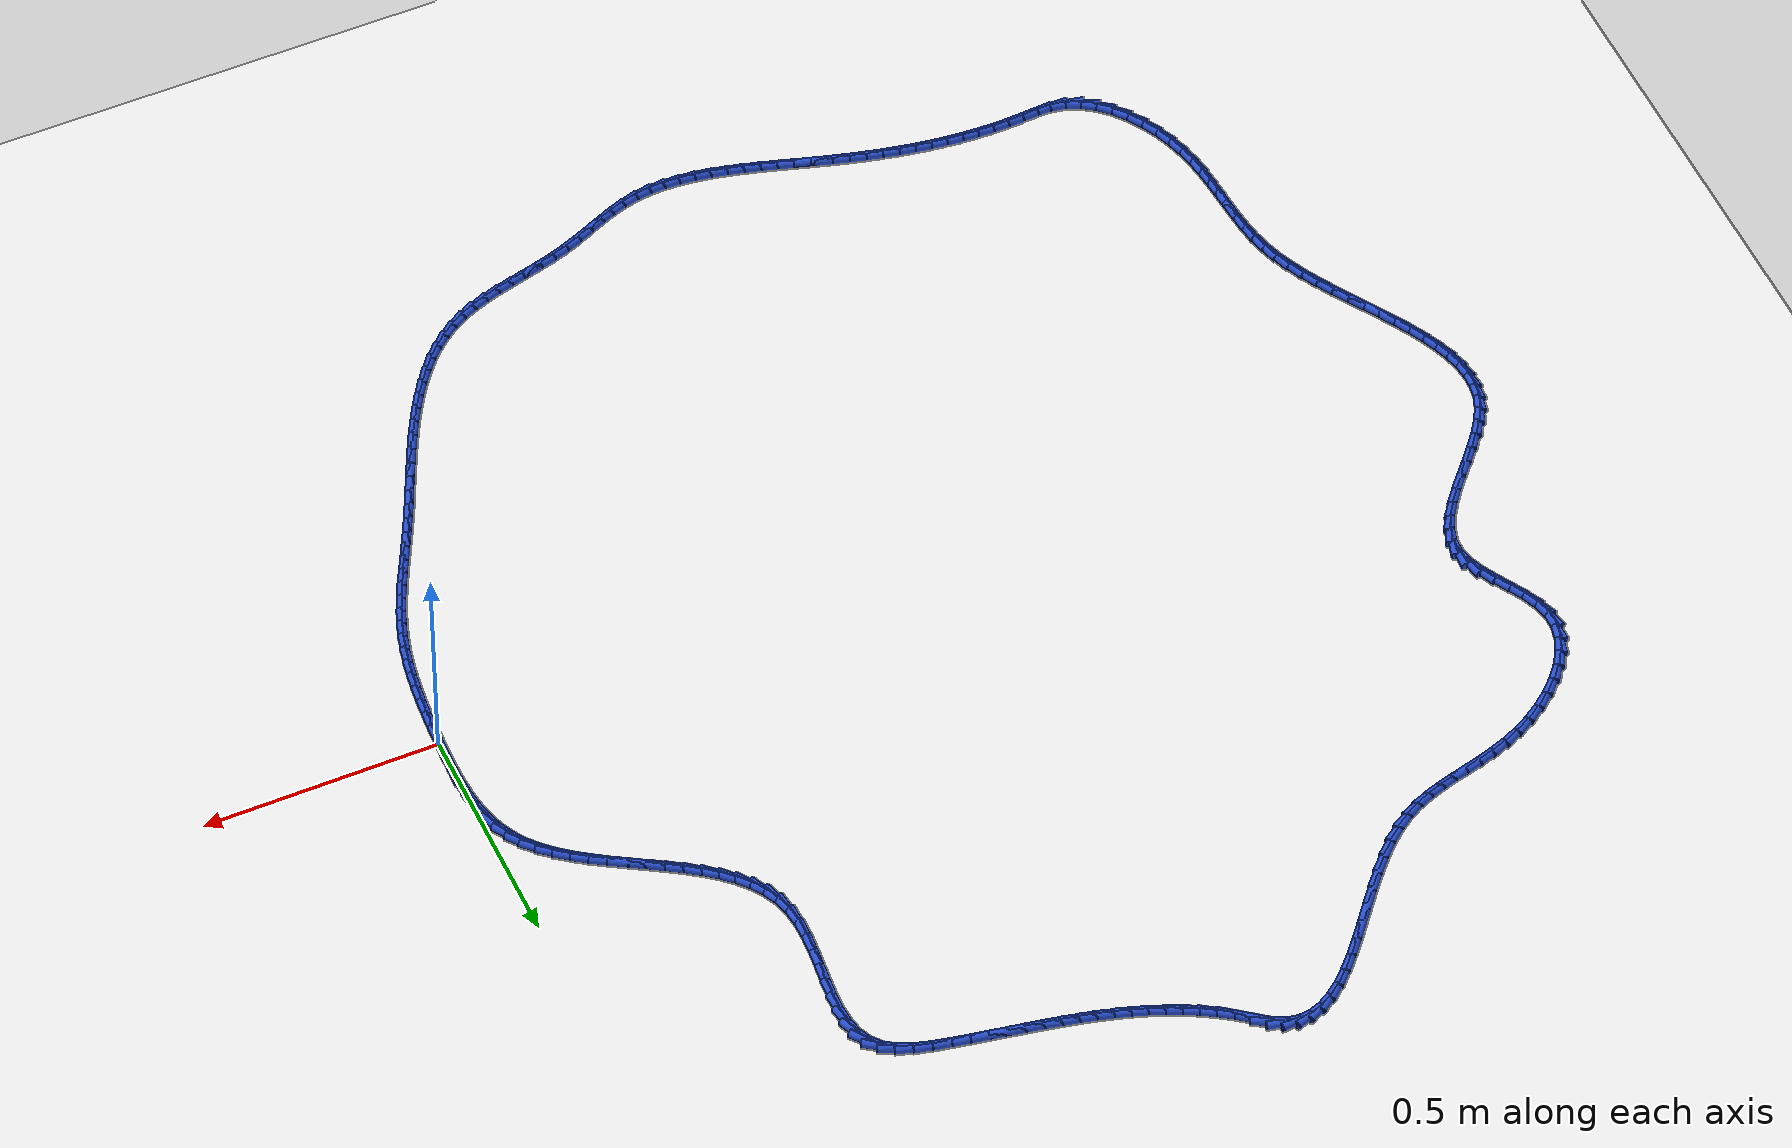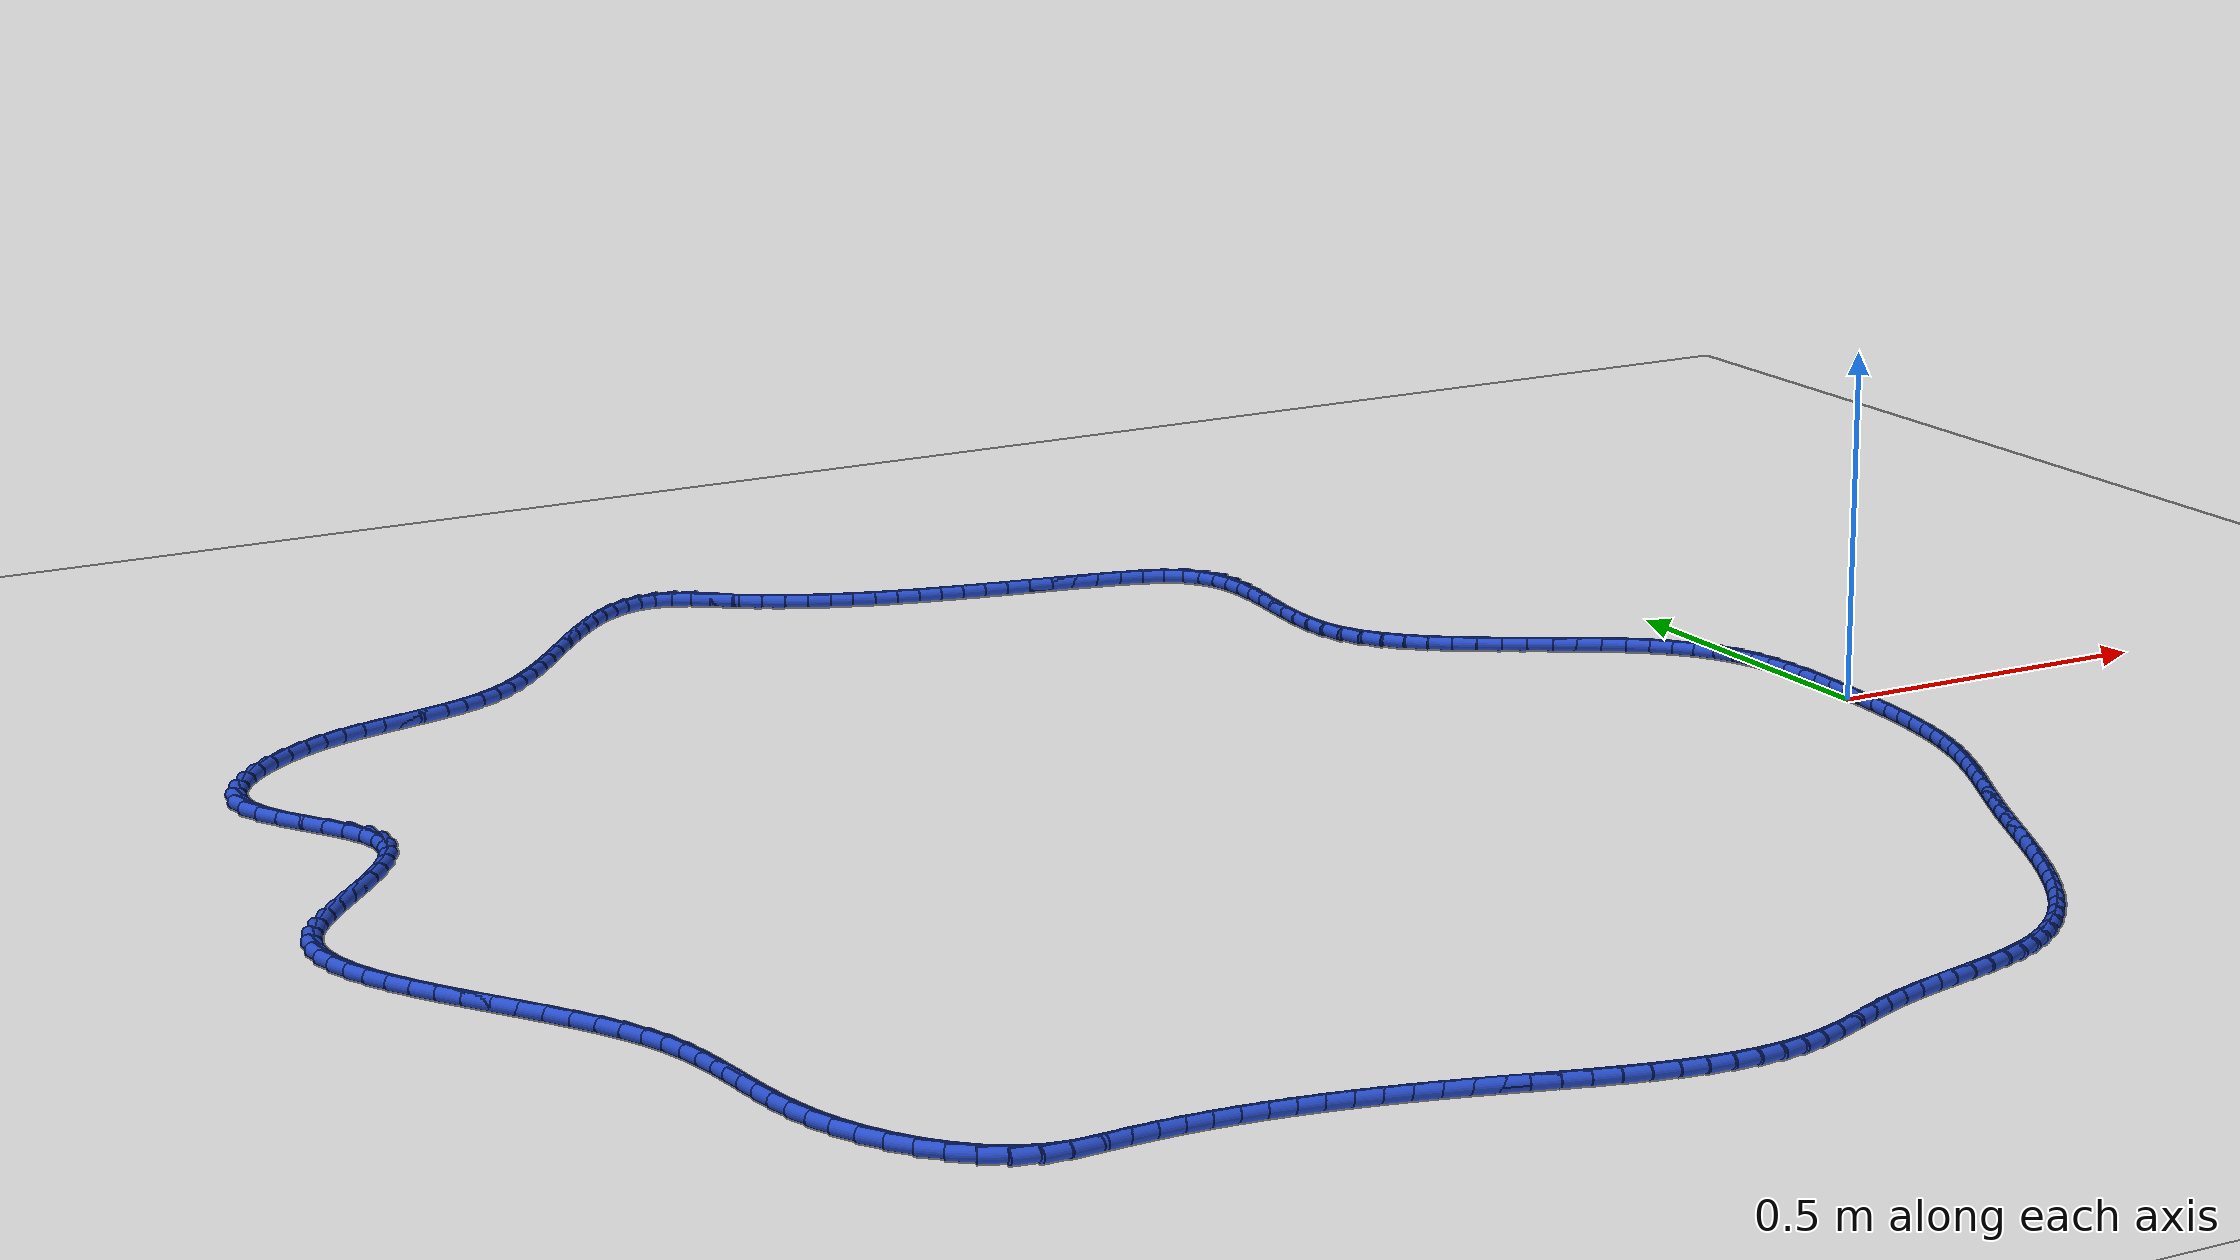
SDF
<sdf version="1.6">
 <world name="default">
  <light name="sun" type="directional">
   <pose>0 0 10 0 -0 0</pose>
   <diffuse>0.8 0.8 0.8 1</diffuse>
   <specular>0.2 0.2 0.2 1</specular>
   <attenuation>
    <range>1000</range>
    <constant>0.9</constant>
    <linear>0.01</linear>
    <quadratic>0.001</quadratic>
   </attenuation>
   <direction>-0.5 0.1 -0.9</direction>
  </light>
  <model name="ground_plane">
   <static>1</static>
   <link name="link">
    <collision name="collision">
     <geometry><plane><normal>0 0 1</normal><size>100 100</size></plane></geometry>
     <surface><friction><ode><mu>100</mu><mu2>50</mu2></ode></friction></surface>
    </collision>
    <visual name="visual">
     <cast_shadows>0</cast_shadows>
     <geometry><plane><normal>0 0 1</normal><size>100 100</size></plane></geometry>
     <material>
      <script><uri>file://media/materials/scripts/gazebo.material</uri><name>Gazebo/WhiteGlow</name></script>
     </material>
    </visual>
   </link>
  </model>
  <gravity>0 0 -9.8</gravity>
  <magnetic_field>6e-06 2.3e-05 -4.2e-05</magnetic_field>
  <atmosphere type="adiabatic"/>
  <physics name="default_physics" default="0" type="ode">
   <max_step_size>0.001</max_step_size>
   <real_time_factor>1</real_time_factor>
   <real_time_update_rate>1000</real_time_update_rate>
  </physics>
  <scene><ambient>0.4 0.4 0.4 1</ambient><background>0.7 0.7 0.7 1</background><shadows>1</shadows></scene>
  <spherical_coordinates>
   <surface_model>EARTH_WGS84</surface_model>
   <latitude_deg>0</latitude_deg>
   <longitude_deg>0</longitude_deg>
   <elevation>0</elevation>
   <heading_deg>0</heading_deg>
  </spherical_coordinates>
  <model name="line">
   <link name="link_0">
    <pose>1.3010426069826053e-18 5.551115123125783e-17 0.01 0 1.57 1.5289990871327732</pose>
    <collision name="collision">
     <geometry><cylinder><radius>0.01</radius><length>0.08</length></cylinder></geometry>
    </collision>
    <visual name="visual">
     <material>
      <script><name>Gazebo/Blue</name><uri>file://media/materials/scripts/gazebo.material</uri></script>
     </material>
     <geometry><cylinder><radius>0.01</radius><length>0.08</length></cylinder></geometry>
    </visual>
   </link>
   <link name="link_1">
    <pose>0.0015093742879487997 0.03609078575869073 0.01 0 1.57 1.5499851378943492</pose>
    <collision name="collision">
     <geometry><cylinder><radius>0.01</radius><length>0.08</length></cylinder></geometry>
    </collision>
    <visual name="visual">
     <material>
      <script><name>Gazebo/Blue</name><uri>file://media/materials/scripts/gazebo.material</uri></script>
     </material>
     <geometry><cylinder><radius>0.01</radius><length>0.08</length></cylinder></geometry>
    </visual>
   </link>
   <link name="link_2">
    <pose>0.002263017666952617 0.07229893211102216 0.01 0 1.57 -1.5576826322389652</pose>
    <collision name="collision">
     <geometry><cylinder><radius>0.01</radius><length>0.08</length></cylinder></geometry>
    </collision>
    <visual name="visual">
     <material>
      <script><name>Gazebo/Blue</name><uri>file://media/materials/scripts/gazebo.material</uri></script>
     </material>
     <geometry><cylinder><radius>0.01</radius><length>0.08</length></cylinder></geometry>
    </visual>
   </link>
   <link name="link_3">
    <pose>0.0017911209381083473 0.1082819021266612 0.01 0 1.57 -1.5096772794663655</pose>
    <collision name="collision">
     <geometry><cylinder><radius>0.01</radius><length>0.08</length></cylinder></geometry>
    </collision>
    <visual name="visual">
     <material>
      <script><name>Gazebo/Blue</name><uri>file://media/materials/scripts/gazebo.material</uri></script>
     </material>
     <geometry><cylinder><radius>0.01</radius><length>0.08</length></cylinder></geometry>
    </visual>
   </link>
   <link name="link_4">
    <pose>-0.00037612509748710665 0.14369715887527493 0.01 0 1.57 -1.4458912433953883</pose>
    <collision name="collision">
     <geometry><cylinder><radius>0.01</radius><length>0.08</length></cylinder></geometry>
    </collision>
    <visual name="visual">
     <material>
      <script><name>Gazebo/Blue</name><uri>file://media/materials/scripts/gazebo.material</uri></script>
     </material>
     <geometry><cylinder><radius>0.01</radius><length>0.08</length></cylinder></geometry>
    </visual>
   </link>
   <link name="link_5">
    <pose>-0.004708529638736855 0.17820216542653022 0.01 0 1.57 -1.3642533236156058</pose>
    <collision name="collision">
     <geometry><cylinder><radius>0.01</radius><length>0.08</length></cylinder></geometry>
    </collision>
    <visual name="visual">
     <material>
      <script><name>Gazebo/Blue</name><uri>file://media/materials/scripts/gazebo.material</uri></script>
     </material>
     <geometry><cylinder><radius>0.01</radius><length>0.08</length></cylinder></geometry>
    </visual>
   </link>
   <link name="link_6">
    <pose>-0.011675901884543982 0.21145438485009402 0.01 0 1.57 -1.2627578702750764</pose>
    <collision name="collision">
     <geometry><cylinder><radius>0.01</radius><length>0.08</length></cylinder></geometry>
    </collision>
    <visual name="visual">
     <material>
      <script><name>Gazebo/Blue</name><uri>file://media/materials/scripts/gazebo.material</uri></script>
     </material>
     <geometry><cylinder><radius>0.01</radius><length>0.08</length></cylinder></geometry>
    </visual>
   </link>
   <link name="link_7">
    <pose>-0.02174805103381161 0.24311128021563327 0.01 0 1.57 -1.1403248880793007</pose>
    <collision name="collision">
     <geometry><cylinder><radius>0.01</radius><length>0.08</length></cylinder></geometry>
    </collision>
    <visual name="visual">
     <material>
      <script><name>Gazebo/Blue</name><uri>file://media/materials/scripts/gazebo.material</uri></script>
     </material>
     <geometry><cylinder><radius>0.01</radius><length>0.08</length></cylinder></geometry>
    </visual>
   </link>
   <link name="link_8">
    <pose>-0.03539478628544284 0.2728303145928151 0.01 0 1.57 -1.0001608680937926</pose>
    <collision name="collision">
     <geometry><cylinder><radius>0.01</radius><length>0.08</length></cylinder></geometry>
    </collision>
    <visual name="visual">
     <material>
      <script><name>Gazebo/Blue</name><uri>file://media/materials/scripts/gazebo.material</uri></script>
     </material>
     <geometry><cylinder><radius>0.01</radius><length>0.08</length></cylinder></geometry>
    </visual>
   </link>
   <link name="link_9">
    <pose>-0.053029752607261706 0.30030486766787123 0.01 0 1.57 -0.8684000259979132</pose>
    <collision name="collision">
     <geometry><cylinder><radius>0.01</radius><length>0.08</length></cylinder></geometry>
    </collision>
    <visual name="visual">
     <material>
      <script><name>Gazebo/Blue</name><uri>file://media/materials/scripts/gazebo.material</uri></script>
     </material>
     <geometry><cylinder><radius>0.01</radius><length>0.08</length></cylinder></geometry>
    </visual>
   </link>
   <link name="link_10">
    <pose>-0.07445553293797326 0.32561908884248497 0.01 0 1.57 -0.7611738528342561</pose>
    <collision name="collision">
     <geometry><cylinder><radius>0.01</radius><length>0.08</length></cylinder></geometry>
    </collision>
    <visual name="visual">
     <material>
      <script><name>Gazebo/Blue</name><uri>file://media/materials/scripts/gazebo.material</uri></script>
     </material>
     <geometry><cylinder><radius>0.01</radius><length>0.08</length></cylinder></geometry>
    </visual>
   </link>
   <link name="link_11">
    <pose>-0.09909947850621165 0.3490970854630085 0.01 0 1.57 -0.6779099228716905</pose>
    <collision name="collision">
     <geometry><cylinder><radius>0.01</radius><length>0.08</length></cylinder></geometry>
    </collision>
    <visual name="visual">
     <material>
      <script><name>Gazebo/Blue</name><uri>file://media/materials/scripts/gazebo.material</uri></script>
     </material>
     <geometry><cylinder><radius>0.01</radius><length>0.08</length></cylinder></geometry>
    </visual>
   </link>
   <link name="link_12">
    <pose>-0.12638348751876943 0.37106645204353145 0.01 0 1.57 -0.6163332840438137</pose>
    <collision name="collision">
     <geometry><cylinder><radius>0.01</radius><length>0.08</length></cylinder></geometry>
    </collision>
    <visual name="visual">
     <material>
      <script><name>Gazebo/Blue</name><uri>file://media/materials/scripts/gazebo.material</uri></script>
     </material>
     <geometry><cylinder><radius>0.01</radius><length>0.08</length></cylinder></geometry>
    </visual>
   </link>
   <link name="link_13">
    <pose>-0.15572945818243913 0.3918547830981433 0.01 0 1.57 -0.5739887044337283</pose>
    <collision name="collision">
     <geometry><cylinder><radius>0.01</radius><length>0.08</length></cylinder></geometry>
    </collision>
    <visual name="visual">
     <material>
      <script><name>Gazebo/Blue</name><uri>file://media/materials/scripts/gazebo.material</uri></script>
     </material>
     <geometry><cylinder><radius>0.01</radius><length>0.08</length></cylinder></geometry>
    </visual>
   </link>
   <link name="link_14">
    <pose>-0.18655928870401312 0.4117896731409338 0.01 0 1.57 -0.5488951339359027</pose>
    <collision name="collision">
     <geometry><cylinder><radius>0.01</radius><length>0.08</length></cylinder></geometry>
    </collision>
    <visual name="visual">
     <material>
      <script><name>Gazebo/Blue</name><uri>file://media/materials/scripts/gazebo.material</uri></script>
     </material>
     <geometry><cylinder><radius>0.01</radius><length>0.08</length></cylinder></geometry>
    </visual>
   </link>
   <link name="link_15">
    <pose>-0.21829487729028416 0.43119871668599224 0.01 0 1.57 -0.5397965242602958</pose>
    <collision name="collision">
     <geometry><cylinder><radius>0.01</radius><length>0.08</length></cylinder></geometry>
    </collision>
    <visual name="visual">
     <material>
      <script><name>Gazebo/Blue</name><uri>file://media/materials/scripts/gazebo.material</uri></script>
     </material>
     <geometry><cylinder><radius>0.01</radius><length>0.08</length></cylinder></geometry>
    </visual>
   </link>
   <link name="link_16">
    <pose>-0.2503581221480445 0.4504095082474082 0.01 0 1.57 -0.5462340969510177</pose>
    <collision name="collision">
     <geometry><cylinder><radius>0.01</radius><length>0.08</length></cylinder></geometry>
    </collision>
    <visual name="visual">
     <material>
      <script><name>Gazebo/Blue</name><uri>file://media/materials/scripts/gazebo.material</uri></script>
     </material>
     <geometry><cylinder><radius>0.01</radius><length>0.08</length></cylinder></geometry>
    </visual>
   </link>
   <link name="link_17">
    <pose>-0.2821709214840868 0.4697496423392714 0.01 0 1.57 -0.5685606857905623</pose>
    <collision name="collision">
     <geometry><cylinder><radius>0.01</radius><length>0.08</length></cylinder></geometry>
    </collision>
    <visual name="visual">
     <material>
      <script><name>Gazebo/Blue</name><uri>file://media/materials/scripts/gazebo.material</uri></script>
     </material>
     <geometry><cylinder><radius>0.01</radius><length>0.08</length></cylinder></geometry>
    </visual>
   </link>
   <link name="link_18">
    <pose>-0.3131551735052034 0.48954671347567114 0.01 0 1.57 -0.6079359270252546</pose>
    <collision name="collision">
     <geometry><cylinder><radius>0.01</radius><length>0.08</length></cylinder></geometry>
    </collision>
    <visual name="visual">
     <material>
      <script><name>Gazebo/Blue</name><uri>file://media/materials/scripts/gazebo.material</uri></script>
     </material>
     <geometry><cylinder><radius>0.01</radius><length>0.08</length></cylinder></geometry>
    </visual>
   </link>
   <link name="link_19">
    <pose>-0.34273277641818695 0.5101283161706972 0.01 0 1.57 -0.6662746001012232</pose>
    <collision name="collision">
     <geometry><cylinder><radius>0.01</radius><length>0.08</length></cylinder></geometry>
    </collision>
    <visual name="visual">
     <material>
      <script><name>Gazebo/Blue</name><uri>file://media/materials/scripts/gazebo.material</uri></script>
     </material>
     <geometry><cylinder><radius>0.01</radius><length>0.08</length></cylinder></geometry>
    </visual>
   </link>
   <link name="link_20">
    <pose>-0.37032562842982986 0.5318220449384388 0.01 0 1.57 -0.7460411265431658</pose>
    <collision name="collision">
     <geometry><cylinder><radius>0.01</radius><length>0.08</length></cylinder></geometry>
    </collision>
    <visual name="visual">
     <material>
      <script><name>Gazebo/Blue</name><uri>file://media/materials/scripts/gazebo.material</uri></script>
     </material>
     <geometry><cylinder><radius>0.01</radius><length>0.08</length></cylinder></geometry>
    </visual>
   </link>
   <link name="link_21">
    <pose>-0.39535562774692473 0.5549554942929857 0.01 0 1.57 -0.8496764899215774</pose>
    <collision name="collision">
     <geometry><cylinder><radius>0.01</radius><length>0.08</length></cylinder></geometry>
    </collision>
    <visual name="visual">
     <material>
      <script><name>Gazebo/Blue</name><uri>file://media/materials/scripts/gazebo.material</uri></script>
     </material>
     <geometry><cylinder><radius>0.01</radius><length>0.08</length></cylinder></geometry>
    </visual>
   </link>
   <link name="link_22">
    <pose>-0.41724467257626396 0.5798562587484275 0.01 0 1.57 -0.978373477867756</pose>
    <collision name="collision">
     <geometry><cylinder><radius>0.01</radius><length>0.08</length></cylinder></geometry>
    </collision>
    <visual name="visual">
     <material>
      <script><name>Gazebo/Blue</name><uri>file://media/materials/scripts/gazebo.material</uri></script>
     </material>
     <geometry><cylinder><radius>0.01</radius><length>0.08</length></cylinder></geometry>
    </visual>
   </link>
   <link name="link_23">
    <pose>-0.4354146611246403 0.6068519328188539 0.01 0 1.57 -1.1301474944746117</pose>
    <collision name="collision">
     <geometry><cylinder><radius>0.01</radius><length>0.08</length></cylinder></geometry>
    </collision>
    <visual name="visual">
     <material>
      <script><name>Gazebo/Blue</name><uri>file://media/materials/scripts/gazebo.material</uri></script>
     </material>
     <geometry><cylinder><radius>0.01</radius><length>0.08</length></cylinder></geometry>
    </visual>
   </link>
   <link name="link_24">
    <pose>-0.44928749159884596 0.636270111018354 0.01 0 1.57 -1.2978316115861905</pose>
    <collision name="collision">
     <geometry><cylinder><radius>0.01</radius><length>0.08</length></cylinder></geometry>
    </collision>
    <visual name="visual">
     <material>
      <script><name>Gazebo/Blue</name><uri>file://media/materials/scripts/gazebo.material</uri></script>
     </material>
     <geometry><cylinder><radius>0.01</radius><length>0.08</length></cylinder></geometry>
    </visual>
   </link>
   <link name="link_25">
    <pose>-0.45829190780061263 0.6684341893582361 0.01 0 1.57 -1.452235611223432</pose>
    <collision name="collision">
     <geometry><cylinder><radius>0.01</radius><length>0.08</length></cylinder></geometry>
    </collision>
    <visual name="visual">
     <material>
      <script><name>Gazebo/Blue</name><uri>file://media/materials/scripts/gazebo.material</uri></script>
     </material>
     <geometry><cylinder><radius>0.01</radius><length>0.08</length></cylinder></geometry>
    </visual>
   </link>
   <link name="link_26">
    <pose>-0.46244584084719786 0.7033062067135757 0.01 0 1.57 -1.5611669726235993</pose>
    <collision name="collision">
     <geometry><cylinder><radius>0.01</radius><length>0.08</length></cylinder></geometry>
    </collision>
    <visual name="visual">
     <material>
      <script><name>Gazebo/Blue</name><uri>file://media/materials/scripts/gazebo.material</uri></script>
     </material>
     <geometry><cylinder><radius>0.01</radius><length>0.08</length></cylinder></geometry>
    </visual>
   </link>
   <link name="link_27">
    <pose>-0.4628012502126478 0.7402140173530468 0.01 0 1.57 1.5110250331409731</pose>
    <collision name="collision">
     <geometry><cylinder><radius>0.01</radius><length>0.08</length></cylinder></geometry>
    </collision>
    <visual name="visual">
     <material>
      <script><name>Gazebo/Blue</name><uri>file://media/materials/scripts/gazebo.material</uri></script>
     </material>
     <geometry><cylinder><radius>0.01</radius><length>0.08</length></cylinder></geometry>
    </visual>
   </link>
   <link name="link_28">
    <pose>-0.4605148316582588 0.7784212392594733 0.01 0 1.57 1.4738219561894088</pose>
    <collision name="collision">
     <geometry><cylinder><radius>0.01</radius><length>0.08</length></cylinder></geometry>
    </collision>
    <visual name="visual">
     <material>
      <script><name>Gazebo/Blue</name><uri>file://media/materials/scripts/gazebo.material</uri></script>
     </material>
     <geometry><cylinder><radius>0.01</radius><length>0.08</length></cylinder></geometry>
    </visual>
   </link>
   <link name="link_29">
    <pose>-0.4567432809453266 0.8171914904156784 0.01 0 1.57 1.4649673731915769</pose>
    <collision name="collision">
     <geometry><cylinder><radius>0.01</radius><length>0.08</length></cylinder></geometry>
    </collision>
    <visual name="visual">
     <material>
      <script><name>Gazebo/Blue</name><uri>file://media/materials/scripts/gazebo.material</uri></script>
     </material>
     <geometry><cylinder><radius>0.01</radius><length>0.08</length></cylinder></geometry>
    </visual>
   </link>
   <link name="link_30">
    <pose>-0.4526432938351472 0.8557883888044853 0.01 0 1.57 1.4842006449011578</pose>
    <collision name="collision">
     <geometry><cylinder><radius>0.01</radius><length>0.08</length></cylinder></geometry>
    </collision>
    <visual name="visual">
     <material>
      <script><name>Gazebo/Blue</name><uri>file://media/materials/scripts/gazebo.material</uri></script>
     </material>
     <geometry><cylinder><radius>0.01</radius><length>0.08</length></cylinder></geometry>
    </visual>
   </link>
   <link name="link_31">
    <pose>-0.4493715660890166 0.8934755524087171 0.01 0 1.57 1.535108509654871</pose>
    <collision name="collision">
     <geometry><cylinder><radius>0.01</radius><length>0.08</length></cylinder></geometry>
    </collision>
    <visual name="visual">
     <material>
      <script><name>Gazebo/Blue</name><uri>file://media/materials/scripts/gazebo.material</uri></script>
     </material>
     <geometry><cylinder><radius>0.01</radius><length>0.08</length></cylinder></geometry>
    </visual>
   </link>
   <link name="link_32">
    <pose>-0.4480847934682311 0.9295165992111973 0.01 0 1.57 -1.5157433296709983</pose>
    <collision name="collision">
     <geometry><cylinder><radius>0.01</radius><length>0.08</length></cylinder></geometry>
    </collision>
    <visual name="visual">
     <material>
      <script><name>Gazebo/Blue</name><uri>file://media/materials/scripts/gazebo.material</uri></script>
     </material>
     <geometry><cylinder><radius>0.01</radius><length>0.08</length></cylinder></geometry>
    </visual>
   </link>
   <link name="link_33">
    <pose>-0.4499396717340862 0.9631751471947491 0.01 0 1.57 -1.3719751764933068</pose>
    <collision name="collision">
     <geometry><cylinder><radius>0.01</radius><length>0.08</length></cylinder></geometry>
    </collision>
    <visual name="visual">
     <material>
      <script><name>Gazebo/Blue</name><uri>file://media/materials/scripts/gazebo.material</uri></script>
     </material>
     <geometry><cylinder><radius>0.01</radius><length>0.08</length></cylinder></geometry>
    </visual>
   </link>
   <link name="link_34">
    <pose>-0.4560928966478782 0.9937148143421954 0.01 0 1.57 -1.1604687934787343</pose>
    <collision name="collision">
     <geometry><cylinder><radius>0.01</radius><length>0.08</length></cylinder></geometry>
    </collision>
    <visual name="visual">
     <material>
      <script><name>Gazebo/Blue</name><uri>file://media/materials/scripts/gazebo.material</uri></script>
     </material>
     <geometry><cylinder><radius>0.01</radius><length>0.08</length></cylinder></geometry>
    </visual>
   </link>
   <link name="link_35">
    <pose>-0.4677011639709031 1.02039921863636 0.01 0 1.57 -0.8812132171909178</pose>
    <collision name="collision">
     <geometry><cylinder><radius>0.01</radius><length>0.08</length></cylinder></geometry>
    </collision>
    <visual name="visual">
     <material>
      <script><name>Gazebo/Blue</name><uri>file://media/materials/scripts/gazebo.material</uri></script>
     </material>
     <geometry><cylinder><radius>0.01</radius><length>0.08</length></cylinder></geometry>
    </visual>
   </link>
   <link name="link_36">
    <pose>-0.48592014714834825 1.0424925964372902 0.01 0 1.57 -0.5970859751958797</pose>
    <collision name="collision">
     <geometry><cylinder><radius>0.01</radius><length>0.08</length></cylinder></geometry>
    </collision>
    <visual name="visual">
     <material>
      <script><name>Gazebo/Blue</name><uri>file://media/materials/scripts/gazebo.material</uri></script>
     </material>
     <geometry><cylinder><radius>0.01</radius><length>0.08</length></cylinder></geometry>
    </visual>
   </link>
   <link name="link_37">
    <pose>-0.5112049766916569 1.059682927594205 0.01 0 1.57 -0.40216599644453177</pose>
    <collision name="collision">
     <geometry><cylinder><radius>0.01</radius><length>0.08</length></cylinder></geometry>
    </collision>
    <visual name="visual">
     <material>
      <script><name>Gazebo/Blue</name><uri>file://media/materials/scripts/gazebo.material</uri></script>
     </material>
     <geometry><cylinder><radius>0.01</radius><length>0.08</length></cylinder></geometry>
    </visual>
   </link>
   <link name="link_38">
    <pose>-0.5420901935219287 1.072819915663861 0.01 0 1.57 -0.284102088188988</pose>
    <collision name="collision">
     <geometry><cylinder><radius>0.01</radius><length>0.08</length></cylinder></geometry>
    </collision>
    <visual name="visual">
     <material>
      <script><name>Gazebo/Blue</name><uri>file://media/materials/scripts/gazebo.material</uri></script>
     </material>
     <geometry><cylinder><radius>0.01</radius><length>0.08</length></cylinder></geometry>
    </visual>
   </link>
   <link name="link_39">
    <pose>-0.5767841359382735 1.0829505772163373 0.01 0 1.57 -0.2190154626607884</pose>
    <collision name="collision">
     <geometry><cylinder><radius>0.01</radius><length>0.08</length></cylinder></geometry>
    </collision>
    <visual name="visual">
     <material>
      <script><name>Gazebo/Blue</name><uri>file://media/materials/scripts/gazebo.material</uri></script>
     </material>
     <geometry><cylinder><radius>0.01</radius><length>0.08</length></cylinder></geometry>
    </visual>
   </link>
   <link name="link_40">
    <pose>-0.6134951422398011 1.0911219288217127 0.01 0 1.57 -0.19302854937290198</pose>
    <collision name="collision">
     <geometry><cylinder><radius>0.01</radius><length>0.08</length></cylinder></geometry>
    </collision>
    <visual name="visual">
     <material>
      <script><name>Gazebo/Blue</name><uri>file://media/materials/scripts/gazebo.material</uri></script>
     </material>
     <geometry><cylinder><radius>0.01</radius><length>0.08</length></cylinder></geometry>
    </visual>
   </link>
   <link name="link_41">
    <pose>-0.6504887639221568 1.0983527851125534 0.01 0 1.57 -0.185511469880514</pose>
    <collision name="collision">
     <geometry><cylinder><radius>0.01</radius><length>0.08</length></cylinder></geometry>
    </collision>
    <visual name="visual">
     <material>
      <script><name>Gazebo/Blue</name><uri>file://media/materials/scripts/gazebo.material</uri></script>
     </material>
     <geometry><cylinder><radius>0.01</radius><length>0.08</length></cylinder></geometry>
    </visual>
   </link>
   <link name="link_42">
    <pose>-0.6869695435538838 1.1051991065345077 0.01 0 1.57 -0.18267262407618715</pose>
    <collision name="collision">
     <geometry><cylinder><radius>0.01</radius><length>0.08</length></cylinder></geometry>
    </collision>
    <visual name="visual">
     <material>
      <script><name>Gazebo/Blue</name><uri>file://media/materials/scripts/gazebo.material</uri></script>
     </material>
     <geometry><cylinder><radius>0.01</radius><length>0.08</length></cylinder></geometry>
    </visual>
   </link>
   <link name="link_43">
    <pose>-0.7229097612092996 1.111838414877889 0.01 0 1.57 -0.1843174612936856</pose>
    <collision name="collision">
     <geometry><cylinder><radius>0.01</radius><length>0.08</length></cylinder></geometry>
    </collision>
    <visual name="visual">
     <material>
      <script><name>Gazebo/Blue</name><uri>file://media/materials/scripts/gazebo.material</uri></script>
     </material>
     <geometry><cylinder><radius>0.01</radius><length>0.08</length></cylinder></geometry>
    </visual>
   </link>
   <link name="link_44">
    <pose>-0.7583042235322829 1.1184371279754313 0.01 0 1.57 -0.19064855812285278</pose>
    <collision name="collision">
     <geometry><cylinder><radius>0.01</radius><length>0.08</length></cylinder></geometry>
    </collision>
    <visual name="visual">
     <material>
      <script><name>Gazebo/Blue</name><uri>file://media/materials/scripts/gazebo.material</uri></script>
     </material>
     <geometry><cylinder><radius>0.01</radius><length>0.08</length></cylinder></geometry>
    </visual>
   </link>
   <link name="link_45">
    <pose>-0.7931477371667132 1.1251616636598702 0.01 0 1.57 -0.2018589244967569</pose>
    <collision name="collision">
     <geometry><cylinder><radius>0.01</radius><length>0.08</length></cylinder></geometry>
    </collision>
    <visual name="visual">
     <material>
      <script><name>Gazebo/Blue</name><uri>file://media/materials/scripts/gazebo.material</uri></script>
     </material>
     <geometry><cylinder><radius>0.01</radius><length>0.08</length></cylinder></geometry>
    </visual>
   </link>
   <link name="link_46">
    <pose>-0.82743510875647 1.1321784397639407 0.01 0 1.57 -0.2181252372307707</pose>
    <collision name="collision">
     <geometry><cylinder><radius>0.01</radius><length>0.08</length></cylinder></geometry>
    </collision>
    <visual name="visual">
     <material>
      <script><name>Gazebo/Blue</name><uri>file://media/materials/scripts/gazebo.material</uri></script>
     </material>
     <geometry><cylinder><radius>0.01</radius><length>0.08</length></cylinder></geometry>
    </visual>
   </link>
   <link name="link_47">
    <pose>-0.8611611449454323 1.139653874120378 0.01 0 1.57 -0.23959663805163278</pose>
    <collision name="collision">
     <geometry><cylinder><radius>0.01</radius><length>0.08</length></cylinder></geometry>
    </collision>
    <visual name="visual">
     <material>
      <script><name>Gazebo/Blue</name><uri>file://media/materials/scripts/gazebo.material</uri></script>
     </material>
     <geometry><cylinder><radius>0.01</radius><length>0.08</length></cylinder></geometry>
    </visual>
   </link>
   <link name="link_48">
    <pose>-0.8943206523774799 1.1477543845619171 0.01 0 1.57 -0.2663784753518847</pose>
    <collision name="collision">
     <geometry><cylinder><radius>0.01</radius><length>0.08</length></cylinder></geometry>
    </collision>
    <visual name="visual">
     <material>
      <script><name>Gazebo/Blue</name><uri>file://media/materials/scripts/gazebo.material</uri></script>
     </material>
     <geometry><cylinder><radius>0.01</radius><length>0.08</length></cylinder></geometry>
    </visual>
   </link>
   <link name="link_49">
    <pose>-0.926908437696492 1.1566463889212932 0.01 0 1.57 -0.2985108515455796</pose>
    <collision name="collision">
     <geometry><cylinder><radius>0.01</radius><length>0.08</length></cylinder></geometry>
    </collision>
    <visual name="visual">
     <material>
      <script><name>Gazebo/Blue</name><uri>file://media/materials/scripts/gazebo.material</uri></script>
     </material>
     <geometry><cylinder><radius>0.01</radius><length>0.08</length></cylinder></geometry>
    </visual>
   </link>
   <link name="link_50">
    <pose>-0.9589193075463476 1.166496305031241 0.01 0 1.57 -0.3359427284896135</pose>
    <collision name="collision">
     <geometry><cylinder><radius>0.01</radius><length>0.08</length></cylinder></geometry>
    </collision>
    <visual name="visual">
     <material>
      <script><name>Gazebo/Blue</name><uri>file://media/materials/scripts/gazebo.material</uri></script>
     </material>
     <geometry><cylinder><radius>0.01</radius><length>0.08</length></cylinder></geometry>
    </visual>
   </link>
   <link name="link_51">
    <pose>-0.9903480685709265 1.1774705507244958 0.01 0 1.57 -0.378503707828925</pose>
    <collision name="collision">
     <geometry><cylinder><radius>0.01</radius><length>0.08</length></cylinder></geometry>
    </collision>
    <visual name="visual">
     <material>
      <script><name>Gazebo/Blue</name><uri>file://media/materials/scripts/gazebo.material</uri></script>
     </material>
     <geometry><cylinder><radius>0.01</radius><length>0.08</length></cylinder></geometry>
    </visual>
   </link>
   <link name="link_52">
    <pose>-1.0211895274141078 1.189735543833793 0.01 0 1.57 -0.425877337422373</pose>
    <collision name="collision">
     <geometry><cylinder><radius>0.01</radius><length>0.08</length></cylinder></geometry>
    </collision>
    <visual name="visual">
     <material>
      <script><name>Gazebo/Blue</name><uri>file://media/materials/scripts/gazebo.material</uri></script>
     </material>
     <geometry><cylinder><radius>0.01</radius><length>0.08</length></cylinder></geometry>
    </visual>
   </link>
   <link name="link_53">
    <pose>-1.051438490719771 1.2034577021918675 0.01 0 1.57 -0.4775815000869753</pose>
    <collision name="collision">
     <geometry><cylinder><radius>0.01</radius><length>0.08</length></cylinder></geometry>
    </collision>
    <visual name="visual">
     <material>
      <script><name>Gazebo/Blue</name><uri>file://media/materials/scripts/gazebo.material</uri></script>
     </material>
     <geometry><cylinder><radius>0.01</radius><length>0.08</length></cylinder></geometry>
    </visual>
   </link>
   <link name="link_54">
    <pose>-1.0810897651317952 1.2188034436314545 0.01 0 1.57 -0.5329623754756757</pose>
    <collision name="collision">
     <geometry><cylinder><radius>0.01</radius><length>0.08</length></cylinder></geometry>
    </collision>
    <visual name="visual">
     <material>
      <script><name>Gazebo/Blue</name><uri>file://media/materials/scripts/gazebo.material</uri></script>
     </material>
     <geometry><cylinder><radius>0.01</radius><length>0.08</length></cylinder></geometry>
    </visual>
   </link>
   <link name="link_55">
    <pose>-1.11013815729406 1.2359391859852888 0.01 0 1.57 -0.5912077204481779</pose>
    <collision name="collision">
     <geometry><cylinder><radius>0.01</radius><length>0.08</length></cylinder></geometry>
    </collision>
    <visual name="visual">
     <material>
      <script><name>Gazebo/Blue</name><uri>file://media/materials/scripts/gazebo.material</uri></script>
     </material>
     <geometry><cylinder><radius>0.01</radius><length>0.08</length></cylinder></geometry>
    </visual>
   </link>
   <link name="link_56">
    <pose>-1.1385784738504447 1.2550313470861059 0.01 0 1.57 -0.6509662323063921</pose>
    <collision name="collision">
     <geometry><cylinder><radius>0.01</radius><length>0.08</length></cylinder></geometry>
    </collision>
    <visual name="visual">
     <material>
      <script><name>Gazebo/Blue</name><uri>file://media/materials/scripts/gazebo.material</uri></script>
     </material>
     <geometry><cylinder><radius>0.01</radius><length>0.08</length></cylinder></geometry>
    </visual>
   </link>
   <link name="link_57">
    <pose>-1.1664060476502955 1.276228449013121 0.01 0 1.57 -0.6556699043030959</pose>
    <collision name="collision">
     <geometry><cylinder><radius>0.01</radius><length>0.08</length></cylinder></geometry>
    </collision>
    <visual name="visual">
     <material>
      <script><name>Gazebo/Blue</name><uri>file://media/materials/scripts/gazebo.material</uri></script>
     </material>
     <geometry><cylinder><radius>0.01</radius><length>0.08</length></cylinder></geometry>
    </visual>
   </link>
   <link name="link_58">
    <pose>-1.1936886931522523 1.2972139824147146 0.01 0 1.57 -0.48501228219277687</pose>
    <collision name="collision">
     <geometry><cylinder><radius>0.01</radius><length>0.08</length></cylinder></geometry>
    </collision>
    <visual name="visual">
     <material>
      <script><name>Gazebo/Blue</name><uri>file://media/materials/scripts/gazebo.material</uri></script>
     </material>
     <geometry><cylinder><radius>0.01</radius><length>0.08</length></cylinder></geometry>
    </visual>
   </link>
   <link name="link_59">
    <pose>-1.2206261515871513 1.3114099786957087 0.01 0 1.57 -0.20951843793595495</pose>
    <collision name="collision">
     <geometry><cylinder><radius>0.01</radius><length>0.08</length></cylinder></geometry>
    </collision>
    <visual name="visual">
     <material>
      <script><name>Gazebo/Blue</name><uri>file://media/materials/scripts/gazebo.material</uri></script>
     </material>
     <geometry><cylinder><radius>0.01</radius><length>0.08</length></cylinder></geometry>
    </visual>
   </link>
   <link name="link_60">
    <pose>-1.2473273559740614 1.3170876976100212 0.01 0 1.57 0.07556879433054528</pose>
    <collision name="collision">
     <geometry><cylinder><radius>0.01</radius><length>0.08</length></cylinder></geometry>
    </collision>
    <visual name="visual">
     <material>
      <script><name>Gazebo/Blue</name><uri>file://media/materials/scripts/gazebo.material</uri></script>
     </material>
     <geometry><cylinder><radius>0.01</radius><length>0.08</length></cylinder></geometry>
    </visual>
   </link>
   <link name="link_61">
    <pose>-1.273850293239914 1.3150795671908975 0.01 0 1.57 0.32331235466705427</pose>
    <collision name="collision">
     <geometry><cylinder><radius>0.01</radius><length>0.08</length></cylinder></geometry>
    </collision>
    <visual name="visual">
     <material>
      <script><name>Gazebo/Blue</name><uri>file://media/materials/scripts/gazebo.material</uri></script>
     </material>
     <geometry><cylinder><radius>0.01</radius><length>0.08</length></cylinder></geometry>
    </visual>
   </link>
   <link name="link_62">
    <pose>-1.3002526534437602 1.3062329396506094 0.01 0 1.57 0.5130185021952725</pose>
    <collision name="collision">
     <geometry><cylinder><radius>0.01</radius><length>0.08</length></cylinder></geometry>
    </collision>
    <visual name="visual">
     <material>
      <script><name>Gazebo/Blue</name><uri>file://media/materials/scripts/gazebo.material</uri></script>
     </material>
     <geometry><cylinder><radius>0.01</radius><length>0.08</length></cylinder></geometry>
    </visual>
   </link>
   <link name="link_63">
    <pose>-1.32659212664465 1.2913951672014277 0.01 0 1.57 0.6490880651406916</pose>
    <collision name="collision">
     <geometry><cylinder><radius>0.01</radius><length>0.08</length></cylinder></geometry>
    </collision>
    <visual name="visual">
     <material>
      <script><name>Gazebo/Blue</name><uri>file://media/materials/scripts/gazebo.material</uri></script>
     </material>
     <geometry><cylinder><radius>0.01</radius><length>0.08</length></cylinder></geometry>
    </visual>
   </link>
   <link name="link_64">
    <pose>-1.3529264029016337 1.2714136020556235 0.01 0 1.57 0.7438002824619205</pose>
    <collision name="collision">
     <geometry><cylinder><radius>0.01</radius><length>0.08</length></cylinder></geometry>
    </collision>
    <visual name="visual">
     <material>
      <script><name>Gazebo/Blue</name><uri>file://media/materials/scripts/gazebo.material</uri></script>
     </material>
     <geometry><cylinder><radius>0.01</radius><length>0.08</length></cylinder></geometry>
    </visual>
   </link>
   <link name="link_65">
    <pose>-1.379313172273763 1.247135596425469 0.01 0 1.57 0.8080805425991572</pose>
    <collision name="collision">
     <geometry><cylinder><radius>0.01</radius><length>0.08</length></cylinder></geometry>
    </collision>
    <visual name="visual">
     <material>
      <script><name>Gazebo/Blue</name><uri>file://media/materials/scripts/gazebo.material</uri></script>
     </material>
     <geometry><cylinder><radius>0.01</radius><length>0.08</length></cylinder></geometry>
    </visual>
   </link>
   <link name="link_66">
    <pose>-1.4058101248200883 1.2194085025232342 0.01 0 1.57 0.8495977469195756</pose>
    <collision name="collision">
     <geometry><cylinder><radius>0.01</radius><length>0.08</length></cylinder></geometry>
    </collision>
    <visual name="visual">
     <material>
      <script><name>Gazebo/Blue</name><uri>file://media/materials/scripts/gazebo.material</uri></script>
     </material>
     <geometry><cylinder><radius>0.01</radius><length>0.08</length></cylinder></geometry>
    </visual>
   </link>
   <link name="link_67">
    <pose>-1.432474950599659 1.189079672561191 0.01 0 1.57 0.8732250197811251</pose>
    <collision name="collision">
     <geometry><cylinder><radius>0.01</radius><length>0.08</length></cylinder></geometry>
    </collision>
    <visual name="visual">
     <material>
      <script><name>Gazebo/Blue</name><uri>file://media/materials/scripts/gazebo.material</uri></script>
     </material>
     <geometry><cylinder><radius>0.01</radius><length>0.08</length></cylinder></geometry>
    </visual>
   </link>
   <link name="link_68">
    <pose>-1.4593653396715274 1.1569964587516102 0.01 0 1.57 0.8817779321621837</pose>
    <collision name="collision">
     <geometry><cylinder><radius>0.01</radius><length>0.08</length></cylinder></geometry>
    </collision>
    <visual name="visual">
     <material>
      <script><name>Gazebo/Blue</name><uri>file://media/materials/scripts/gazebo.material</uri></script>
     </material>
     <geometry><cylinder><radius>0.01</radius><length>0.08</length></cylinder></geometry>
    </visual>
   </link>
   <link name="link_69">
    <pose>-1.4865389820947428 1.1240062133067636 0.01 0 1.57 0.8765407020072276</pose>
    <collision name="collision">
     <geometry><cylinder><radius>0.01</radius><length>0.08</length></cylinder></geometry>
    </collision>
    <visual name="visual">
     <material>
      <script><name>Gazebo/Blue</name><uri>file://media/materials/scripts/gazebo.material</uri></script>
     </material>
     <geometry><cylinder><radius>0.01</radius><length>0.08</length></cylinder></geometry>
    </visual>
   </link>
   <link name="link_70">
    <pose>-1.5140535679283562 1.0909562884389212 0.01 0 1.57 0.8575452391647471</pose>
    <collision name="collision">
     <geometry><cylinder><radius>0.01</radius><length>0.08</length></cylinder></geometry>
    </collision>
    <visual name="visual">
     <material>
      <script><name>Gazebo/Blue</name><uri>file://media/materials/scripts/gazebo.material</uri></script>
     </material>
     <geometry><cylinder><radius>0.01</radius><length>0.08</length></cylinder></geometry>
    </visual>
   </link>
   <link name="link_71">
    <pose>-1.5419667872314182 1.0586940363603556 0.01 0 1.57 0.8236474292374899</pose>
    <collision name="collision">
     <geometry><cylinder><radius>0.01</radius><length>0.08</length></cylinder></geometry>
    </collision>
    <visual name="visual">
     <material>
      <script><name>Gazebo/Blue</name><uri>file://media/materials/scripts/gazebo.material</uri></script>
     </material>
     <geometry><cylinder><radius>0.01</radius><length>0.08</length></cylinder></geometry>
    </visual>
   </link>
   <link name="link_72">
    <pose>-1.5703363300629802 1.0280668092833372 0.01 0 1.57 0.7724455790134986</pose>
    <collision name="collision">
     <geometry><cylinder><radius>0.01</radius><length>0.08</length></cylinder></geometry>
    </collision>
    <visual name="visual">
     <material>
      <script><name>Gazebo/Blue</name><uri>file://media/materials/scripts/gazebo.material</uri></script>
     </material>
     <geometry><cylinder><radius>0.01</radius><length>0.08</length></cylinder></geometry>
    </visual>
   </link>
   <link name="link_73">
    <pose>-1.5992198864820912 0.9999219594201376 0.01 0 1.57 0.7001051922625913</pose>
    <collision name="collision">
     <geometry><cylinder><radius>0.01</radius><length>0.08</length></cylinder></geometry>
    </collision>
    <visual name="visual">
     <material>
      <script><name>Gazebo/Blue</name><uri>file://media/materials/scripts/gazebo.material</uri></script>
     </material>
     <geometry><cylinder><radius>0.01</radius><length>0.08</length></cylinder></geometry>
    </visual>
   </link>
   <link name="link_74">
    <pose>-1.6286751465478027 0.9751068389830271 0.01 0 1.57 0.6020954955467981</pose>
    <collision name="collision">
     <geometry><cylinder><radius>0.01</radius><length>0.08</length></cylinder></geometry>
    </collision>
    <visual name="visual">
     <material>
      <script><name>Gazebo/Blue</name><uri>file://media/materials/scripts/gazebo.material</uri></script>
     </material>
     <geometry><cylinder><radius>0.01</radius><length>0.08</length></cylinder></geometry>
    </visual>
   </link>
   <link name="link_75">
    <pose>-1.658757115866552 0.9544339830134573 0.01 0 1.57 0.4939117480487549</pose>
    <collision name="collision">
     <geometry><cylinder><radius>0.01</radius><length>0.08</length></cylinder></geometry>
    </collision>
    <visual name="visual">
     <material>
      <script><name>Gazebo/Blue</name><uri>file://media/materials/scripts/gazebo.material</uri></script>
     </material>
     <geometry><cylinder><radius>0.01</radius><length>0.08</length></cylinder></geometry>
    </visual>
   </link>
   <link name="link_76">
    <pose>-1.689458184817036 0.9379038112376392 0.01 0 1.57 0.39982257220621914</pose>
    <collision name="collision">
     <geometry><cylinder><radius>0.01</radius><length>0.08</length></cylinder></geometry>
    </collision>
    <visual name="visual">
     <material>
      <script><name>Gazebo/Blue</name><uri>file://media/materials/scripts/gazebo.material</uri></script>
     </material>
     <geometry><cylinder><radius>0.01</radius><length>0.08</length></cylinder></geometry>
    </visual>
   </link>
   <link name="link_77">
    <pose>-1.7207076397783674 0.9246982887284544 0.01 0 1.57 0.32628874909677225</pose>
    <collision name="collision">
     <geometry><cylinder><radius>0.01</radius><length>0.08</length></cylinder></geometry>
    </collision>
    <visual name="visual">
     <material>
      <script><name>Gazebo/Blue</name><uri>file://media/materials/scripts/gazebo.material</uri></script>
     </material>
     <geometry><cylinder><radius>0.01</radius><length>0.08</length></cylinder></geometry>
    </visual>
   </link>
   <link name="link_78">
    <pose>-1.752431984920827 0.913963295496315 0.01 0 1.57 0.2765663768565235</pose>
    <collision name="collision">
     <geometry><cylinder><radius>0.01</radius><length>0.08</length></cylinder></geometry>
    </collision>
    <visual name="visual">
     <material>
      <script><name>Gazebo/Blue</name><uri>file://media/materials/scripts/gazebo.material</uri></script>
     </material>
     <geometry><cylinder><radius>0.01</radius><length>0.08</length></cylinder></geometry>
    </visual>
   </link>
   <link name="link_79">
    <pose>-1.7845577244146933 0.904844711551633 0.01 0 1.57 0.25200999125385093</pose>
    <collision name="collision">
     <geometry><cylinder><radius>0.01</radius><length>0.08</length></cylinder></geometry>
    </collision>
    <visual name="visual">
     <material>
      <script><name>Gazebo/Blue</name><uri>file://media/materials/scripts/gazebo.material</uri></script>
     </material>
     <geometry><cylinder><radius>0.01</radius><length>0.08</length></cylinder></geometry>
    </visual>
   </link>
   <link name="link_80">
    <pose>-1.8170113624302462 0.8964884169048202 0.01 0 1.57 0.2527646804211723</pose>
    <collision name="collision">
     <geometry><cylinder><radius>0.01</radius><length>0.08</length></cylinder></geometry>
    </collision>
    <visual name="visual">
     <material>
      <script><name>Gazebo/Blue</name><uri>file://media/materials/scripts/gazebo.material</uri></script>
     </material>
     <geometry><cylinder><radius>0.01</radius><length>0.08</length></cylinder></geometry>
    </visual>
   </link>
   <link name="link_81">
    <pose>-1.849719403137765 0.8880402915662887 0.01 0 1.57 0.278221899318455</pose>
    <collision name="collision">
     <geometry><cylinder><radius>0.01</radius><length>0.08</length></cylinder></geometry>
    </collision>
    <visual name="visual">
     <material>
      <script><name>Gazebo/Blue</name><uri>file://media/materials/scripts/gazebo.material</uri></script>
     </material>
     <geometry><cylinder><radius>0.01</radius><length>0.08</length></cylinder></geometry>
    </visual>
   </link>
   <link name="link_82">
    <pose>-1.8826083507075284 0.8786462155464502 0.01 0 1.57 0.3270696576984804</pose>
    <collision name="collision">
     <geometry><cylinder><radius>0.01</radius><length>0.08</length></cylinder></geometry>
    </collision>
    <visual name="visual">
     <material>
      <script><name>Gazebo/Blue</name><uri>file://media/materials/scripts/gazebo.material</uri></script>
     </material>
     <geometry><cylinder><radius>0.01</radius><length>0.08</length></cylinder></geometry>
    </visual>
   </link>
   <link name="link_83">
    <pose>-1.9156047093098176 0.8674520688557166 0.01 0 1.57 0.3970004550298216</pose>
    <collision name="collision">
     <geometry><cylinder><radius>0.01</radius><length>0.08</length></cylinder></geometry>
    </collision>
    <visual name="visual">
     <material>
      <script><name>Gazebo/Blue</name><uri>file://media/materials/scripts/gazebo.material</uri></script>
     </material>
     <geometry><cylinder><radius>0.01</radius><length>0.08</length></cylinder></geometry>
    </visual>
   </link>
   <link name="link_84">
    <pose>-1.9486349831149103 0.8536037315045004 0.01 0 1.57 0.48332251764567724</pose>
    <collision name="collision">
     <geometry><cylinder><radius>0.01</radius><length>0.08</length></cylinder></geometry>
    </collision>
    <visual name="visual">
     <material>
      <script><name>Gazebo/Blue</name><uri>file://media/materials/scripts/gazebo.material</uri></script>
     </material>
     <geometry><cylinder><radius>0.01</radius><length>0.08</length></cylinder></geometry>
    </visual>
   </link>
   <link name="link_85">
    <pose>-1.9815822403161665 0.8363116529851641 0.01 0 1.57 0.5723593689208757</pose>
    <collision name="collision">
     <geometry><cylinder><radius>0.01</radius><length>0.08</length></cylinder></geometry>
    </collision>
    <visual name="visual">
     <material>
      <script><name>Gazebo/Blue</name><uri>file://media/materials/scripts/gazebo.material</uri></script>
     </material>
     <geometry><cylinder><radius>0.01</radius><length>0.08</length></cylinder></geometry>
    </visual>
   </link>
   <link name="link_86">
    <pose>-2.0138235136679787 0.8155385266316577 0.01 0 1.57 0.6613853521207046</pose>
    <collision name="collision">
     <geometry><cylinder><radius>0.01</radius><length>0.08</length></cylinder></geometry>
    </collision>
    <visual name="visual">
     <material>
      <script><name>Gazebo/Blue</name><uri>file://media/materials/scripts/gazebo.material</uri></script>
     </material>
     <geometry><cylinder><radius>0.01</radius><length>0.08</length></cylinder></geometry>
    </visual>
   </link>
   <link name="link_87">
    <pose>-2.0444088420762734 0.7917331364542185 0.01 0 1.57 0.7560950887494892</pose>
    <collision name="collision">
     <geometry><cylinder><radius>0.01</radius><length>0.08</length></cylinder></geometry>
    </collision>
    <visual name="visual">
     <material>
      <script><name>Gazebo/Blue</name><uri>file://media/materials/scripts/gazebo.material</uri></script>
     </material>
     <geometry><cylinder><radius>0.01</radius><length>0.08</length></cylinder></geometry>
    </visual>
   </link>
   <link name="link_88">
    <pose>-2.0723827911678248 0.7653524027322363 0.01 0 1.57 0.862589189192924</pose>
    <collision name="collision">
     <geometry><cylinder><radius>0.01</radius><length>0.08</length></cylinder></geometry>
    </collision>
    <visual name="visual">
     <material>
      <script><name>Gazebo/Blue</name><uri>file://media/materials/scripts/gazebo.material</uri></script>
     </material>
     <geometry><cylinder><radius>0.01</radius><length>0.08</length></cylinder></geometry>
    </visual>
   </link>
   <link name="link_89">
    <pose>-2.0967899265694077 0.7368532457450999 0.01 0 1.57 0.9879119046605255</pose>
    <collision name="collision">
     <geometry><cylinder><radius>0.01</radius><length>0.08</length></cylinder></geometry>
    </collision>
    <visual name="visual">
     <material>
      <script><name>Gazebo/Blue</name><uri>file://media/materials/scripts/gazebo.material</uri></script>
     </material>
     <geometry><cylinder><radius>0.01</radius><length>0.08</length></cylinder></geometry>
    </visual>
   </link>
   <link name="link_90">
    <pose>-2.116674813907799 0.7066925857722001 0.01 0 1.57 1.1402052388294095</pose>
    <collision name="collision">
     <geometry><cylinder><radius>0.01</radius><length>0.08</length></cylinder></geometry>
    </collision>
    <visual name="visual">
     <material>
      <script><name>Gazebo/Blue</name><uri>file://media/materials/scripts/gazebo.material</uri></script>
     </material>
     <geometry><cylinder><radius>0.01</radius><length>0.08</length></cylinder></geometry>
    </visual>
   </link>
   <link name="link_91">
    <pose>-2.131082018809775 0.6753273430929262 0.01 0 1.57 1.3274049931926344</pose>
    <collision name="collision">
     <geometry><cylinder><radius>0.01</radius><length>0.08</length></cylinder></geometry>
    </collision>
    <visual name="visual">
     <material>
      <script><name>Gazebo/Blue</name><uri>file://media/materials/scripts/gazebo.material</uri></script>
     </material>
     <geometry><cylinder><radius>0.01</radius><length>0.08</length></cylinder></geometry>
    </visual>
   </link>
   <link name="link_92">
    <pose>-2.1390561069021095 0.6432144379866683 0.01 0 1.57 1.5527282005152077</pose>
    <collision name="collision">
     <geometry><cylinder><radius>0.01</radius><length>0.08</length></cylinder></geometry>
    </collision>
    <visual name="visual">
     <material>
      <script><name>Gazebo/Blue</name><uri>file://media/materials/scripts/gazebo.material</uri></script>
     </material>
     <geometry><cylinder><radius>0.01</radius><length>0.08</length></cylinder></geometry>
    </visual>
   </link>
   <link name="link_93">
    <pose>-2.139641643811579 0.6108107907328157 0.01 0 1.57 -1.346734347371705</pose>
    <collision name="collision">
     <geometry><cylinder><radius>0.01</radius><length>0.08</length></cylinder></geometry>
    </collision>
    <visual name="visual">
     <material>
      <script><name>Gazebo/Blue</name><uri>file://media/materials/scripts/gazebo.material</uri></script>
     </material>
     <geometry><cylinder><radius>0.01</radius><length>0.08</length></cylinder></geometry>
    </visual>
   </link>
   <link name="link_94">
    <pose>-2.132284162121867 0.5785253347191577 0.01 0 1.57 -1.1706953274929024</pose>
    <collision name="collision">
     <geometry><cylinder><radius>0.01</radius><length>0.08</length></cylinder></geometry>
    </collision>
    <visual name="visual">
     <material>
      <script><name>Gazebo/Blue</name><uri>file://media/materials/scripts/gazebo.material</uri></script>
     </material>
     <geometry><cylinder><radius>0.01</radius><length>0.08</length></cylinder></geometry>
    </visual>
   </link>
   <link name="link_95">
    <pose>-2.1187363987399475 0.5464908819178498 0.01 0 1.57 -1.0752447110821939</pose>
    <collision name="collision">
     <geometry><cylinder><radius>0.01</radius><length>0.08</length></cylinder></geometry>
    </collision>
    <visual name="visual">
     <material>
      <script><name>Gazebo/Blue</name><uri>file://media/materials/scripts/gazebo.material</uri></script>
     </material>
     <geometry><cylinder><radius>0.01</radius><length>0.08</length></cylinder></geometry>
    </visual>
   </link>
   <link name="link_96">
    <pose>-2.1015746703369684 0.5147416799874882 0.01 0 1.57 -1.0459495813716468</pose>
    <collision name="collision">
     <geometry><cylinder><radius>0.01</radius><length>0.08</length></cylinder></geometry>
    </collision>
    <visual name="visual">
     <material>
      <script><name>Gazebo/Blue</name><uri>file://media/materials/scripts/gazebo.material</uri></script>
     </material>
     <geometry><cylinder><radius>0.01</radius><length>0.08</length></cylinder></geometry>
    </visual>
   </link>
   <link name="link_97">
    <pose>-2.083376316254017 0.4833118541956559 0.01 0 1.57 -1.078746913650259</pose>
    <collision name="collision">
     <geometry><cylinder><radius>0.01</radius><length>0.08</length></cylinder></geometry>
    </collision>
    <visual name="visual">
     <material>
      <script><name>Gazebo/Blue</name><uri>file://media/materials/scripts/gazebo.material</uri></script>
     </material>
     <geometry><cylinder><radius>0.01</radius><length>0.08</length></cylinder></geometry>
    </visual>
   </link>
   <link name="link_98">
    <pose>-2.0667186758321807 0.452235529809936 0.01 0 1.57 -1.1828930311923374</pose>
    <collision name="collision">
     <geometry><cylinder><radius>0.01</radius><length>0.08</length></cylinder></geometry>
    </collision>
    <visual name="visual">
     <material>
      <script><name>Gazebo/Blue</name><uri>file://media/materials/scripts/gazebo.material</uri></script>
     </material>
     <geometry><cylinder><radius>0.01</radius><length>0.08</length></cylinder></geometry>
    </visual>
   </link>
   <link name="link_99">
    <pose>-2.054179088412547 0.42154683209791277 0.01 0 1.57 -1.3796131506686444</pose>
    <collision name="collision">
     <geometry><cylinder><radius>0.01</radius><length>0.08</length></cylinder></geometry>
    </collision>
    <visual name="visual">
     <material>
      <script><name>Gazebo/Blue</name><uri>file://media/materials/scripts/gazebo.material</uri></script>
     </material>
     <geometry><cylinder><radius>0.01</radius><length>0.08</length></cylinder></geometry>
    </visual>
   </link>
   <link name="link_100">
    <pose>-2.0483209366048793 0.39127950619551927 0.01 0 1.57 1.5001135467842754</pose>
    <collision name="collision">
     <geometry><cylinder><radius>0.01</radius><length>0.08</length></cylinder></geometry>
    </collision>
    <visual name="visual">
     <material>
      <script><name>Gazebo/Blue</name><uri>file://media/materials/scripts/gazebo.material</uri></script>
     </material>
     <geometry><cylinder><radius>0.01</radius><length>0.08</length></cylinder></geometry>
    </visual>
   </link>
   <link name="link_101">
    <pose>-2.050434118421302 0.36143261205418964 0.01 0 1.57 1.2715462661811854</pose>
    <collision name="collision">
     <geometry><cylinder><radius>0.01</radius><length>0.08</length></cylinder></geometry>
    </collision>
    <visual name="visual">
     <material>
      <script><name>Gazebo/Blue</name><uri>file://media/materials/scripts/gazebo.material</uri></script>
     </material>
     <geometry><cylinder><radius>0.01</radius><length>0.08</length></cylinder></geometry>
    </visual>
   </link>
   <link name="link_102">
    <pose>-2.0595320348695165 0.33194320595545873 0.01 0 1.57 1.1000681692464156</pose>
    <collision name="collision">
     <geometry><cylinder><radius>0.01</radius><length>0.08</length></cylinder></geometry>
    </collision>
    <visual name="visual">
     <material>
      <script><name>Gazebo/Blue</name><uri>file://media/materials/scripts/gazebo.material</uri></script>
     </material>
     <geometry><cylinder><radius>0.01</radius><length>0.08</length></cylinder></geometry>
    </visual>
   </link>
   <link name="link_103">
    <pose>-2.0743920541367236 0.30274191548754104 0.01 0 1.57 0.9809378001997049</pose>
    <collision name="collision">
     <geometry><cylinder><radius>0.01</radius><length>0.08</length></cylinder></geometry>
    </collision>
    <visual name="visual">
     <material>
      <script><name>Gazebo/Blue</name><uri>file://media/materials/scripts/gazebo.material</uri></script>
     </material>
     <geometry><cylinder><radius>0.01</radius><length>0.08</length></cylinder></geometry>
    </visual>
   </link>
   <link name="link_104">
    <pose>-2.0937915444101263 0.2737593682386502 0.01 0 1.57 0.9035055700542058</pose>
    <collision name="collision">
     <geometry><cylinder><radius>0.01</radius><length>0.08</length></cylinder></geometry>
    </collision>
    <visual name="visual">
     <material>
      <script><name>Gazebo/Blue</name><uri>file://media/materials/scripts/gazebo.material</uri></script>
     </material>
     <geometry><cylinder><radius>0.01</radius><length>0.08</length></cylinder></geometry>
    </visual>
   </link>
   <link name="link_105">
    <pose>-2.1165078738769263 0.24492619179700145 0.01 0 1.57 0.8588722297505141</pose>
    <collision name="collision">
     <geometry><cylinder><radius>0.01</radius><length>0.08</length></cylinder></geometry>
    </collision>
    <visual name="visual">
     <material>
      <script><name>Gazebo/Blue</name><uri>file://media/materials/scripts/gazebo.material</uri></script>
     </material>
     <geometry><cylinder><radius>0.01</radius><length>0.08</length></cylinder></geometry>
    </visual>
   </link>
   <link name="link_106">
    <pose>-2.141318410724327 0.21617301375080805 0.01 0 1.57 0.8415715909017297</pose>
    <collision name="collision">
     <geometry><cylinder><radius>0.01</radius><length>0.08</length></cylinder></geometry>
    </collision>
    <visual name="visual">
     <material>
      <script><name>Gazebo/Blue</name><uri>file://media/materials/scripts/gazebo.material</uri></script>
     </material>
     <geometry><cylinder><radius>0.01</radius><length>0.08</length></cylinder></geometry>
    </visual>
   </link>
   <link name="link_107">
    <pose>-2.1670005231395306 0.18743046168828503 0.01 0 1.57 0.8494171810909352</pose>
    <collision name="collision">
     <geometry><cylinder><radius>0.01</radius><length>0.08</length></cylinder></geometry>
    </collision>
    <visual name="visual">
     <material>
      <script><name>Gazebo/Blue</name><uri>file://media/materials/scripts/gazebo.material</uri></script>
     </material>
     <geometry><cylinder><radius>0.01</radius><length>0.08</length></cylinder></geometry>
    </visual>
   </link>
   <link name="link_108">
    <pose>-2.1923315793097395 0.15862916319764603 0.01 0 1.57 0.8832506133958559</pose>
    <collision name="collision">
     <geometry><cylinder><radius>0.01</radius><length>0.08</length></cylinder></geometry>
    </collision>
    <visual name="visual">
     <material>
      <script><name>Gazebo/Blue</name><uri>file://media/materials/scripts/gazebo.material</uri></script>
     </material>
     <geometry><cylinder><radius>0.01</radius><length>0.08</length></cylinder></geometry>
    </visual>
   </link>
   <link name="link_109">
    <pose>-2.216088947422156 0.12969974586710592 0.01 0 1.57 0.9470067926473229</pose>
    <collision name="collision">
     <geometry><cylinder><radius>0.01</radius><length>0.08</length></cylinder></geometry>
    </collision>
    <visual name="visual">
     <material>
      <script><name>Gazebo/Blue</name><uri>file://media/materials/scripts/gazebo.material</uri></script>
     </material>
     <geometry><cylinder><radius>0.01</radius><length>0.08</length></cylinder></geometry>
    </visual>
   </link>
   <link name="link_110">
    <pose>-2.2370499956639827 0.10057283728487829 0.01 0 1.57 1.047922644759453</pose>
    <collision name="collision">
     <geometry><cylinder><radius>0.01</radius><length>0.08</length></cylinder></geometry>
    </collision>
    <visual name="visual">
     <material>
      <script><name>Gazebo/Blue</name><uri>file://media/materials/scripts/gazebo.material</uri></script>
     </material>
     <geometry><cylinder><radius>0.01</radius><length>0.08</length></cylinder></geometry>
    </visual>
   </link>
   <link name="link_111">
    <pose>-2.253992092222421 0.07117906503917809 0.01 0 1.57 1.1947114491195927</pose>
    <collision name="collision">
     <geometry><cylinder><radius>0.01</radius><length>0.08</length></cylinder></geometry>
    </collision>
    <visual name="visual">
     <material>
      <script><name>Gazebo/Blue</name><uri>file://media/materials/scripts/gazebo.material</uri></script>
     </material>
     <geometry><cylinder><radius>0.01</radius><length>0.08</length></cylinder></geometry>
    </visual>
   </link>
   <link name="link_112">
    <pose>-2.265731113459261 0.04145099882153578 0.01 0 1.57 1.3675122147352388</pose>
    <collision name="collision">
     <geometry><cylinder><radius>0.01</radius><length>0.08</length></cylinder></geometry>
    </collision>
    <visual name="visual">
     <material>
      <script><name>Gazebo/Blue</name><uri>file://media/materials/scripts/gazebo.material</uri></script>
     </material>
     <geometry><cylinder><radius>0.01</radius><length>0.08</length></cylinder></geometry>
    </visual>
   </link>
   <link name="link_113">
    <pose>-2.271932972018227 0.011364078656862493 0.01 0 1.57 1.532649960280038</pose>
    <collision name="collision">
     <geometry><cylinder><radius>0.01</radius><length>0.08</length></cylinder></geometry>
    </collision>
    <visual name="visual">
     <material>
      <script><name>Gazebo/Blue</name><uri>file://media/materials/scripts/gazebo.material</uri></script>
     </material>
     <geometry><cylinder><radius>0.01</radius><length>0.08</length></cylinder></geometry>
    </visual>
   </link>
   <link name="link_114">
    <pose>-2.2730942697639382 -0.019064360837204166 0.01 0 1.57 -1.4623478005615613</pose>
    <collision name="collision">
     <geometry><cylinder><radius>0.01</radius><length>0.08</length></cylinder></geometry>
    </collision>
    <visual name="visual">
     <material>
      <script><name>Gazebo/Blue</name><uri>file://media/materials/scripts/gazebo.material</uri></script>
     </material>
     <geometry><cylinder><radius>0.01</radius><length>0.08</length></cylinder></geometry>
    </visual>
   </link>
   <link name="link_115">
    <pose>-2.269746246680412 -0.04981523812026633 0.01 0 1.57 -1.339119124874484</pose>
    <collision name="collision">
     <geometry><cylinder><radius>0.01</radius><length>0.08</length></cylinder></geometry>
    </collision>
    <visual name="visual">
     <material>
      <script><name>Gazebo/Blue</name><uri>file://media/materials/scripts/gazebo.material</uri></script>
     </material>
     <geometry><cylinder><radius>0.01</radius><length>0.08</length></cylinder></geometry>
    </visual>
   </link>
   <link name="link_116">
    <pose>-2.26242014275166 -0.08086947165192829 0.01 0 1.57 -1.2396907590434736</pose>
    <collision name="collision">
     <geometry><cylinder><radius>0.01</radius><length>0.08</length></cylinder></geometry>
    </collision>
    <visual name="visual">
     <material>
      <script><name>Gazebo/Blue</name><uri>file://media/materials/scripts/gazebo.material</uri></script>
     </material>
     <geometry><cylinder><radius>0.01</radius><length>0.08</length></cylinder></geometry>
    </visual>
   </link>
   <link name="link_117">
    <pose>-2.2516471979616983 -0.1122079798917936 0.01 0 1.57 -1.1620587799954392</pose>
    <collision name="collision">
     <geometry><cylinder><radius>0.01</radius><length>0.08</length></cylinder></geometry>
    </collision>
    <visual name="visual">
     <material>
      <script><name>Gazebo/Blue</name><uri>file://media/materials/scripts/gazebo.material</uri></script>
     </material>
     <geometry><cylinder><radius>0.01</radius><length>0.08</length></cylinder></geometry>
    </visual>
   </link>
   <link name="link_118">
    <pose>-2.2379586522945414 -0.14381168129946664 0.01 0 1.57 -1.1034381833860611</pose>
    <collision name="collision">
     <geometry><cylinder><radius>0.01</radius><length>0.08</length></cylinder></geometry>
    </collision>
    <visual name="visual">
     <material>
      <script><name>Gazebo/Blue</name><uri>file://media/materials/scripts/gazebo.material</uri></script>
     </material>
     <geometry><cylinder><radius>0.01</radius><length>0.08</length></cylinder></geometry>
    </visual>
   </link>
   <link name="link_119">
    <pose>-2.221885745734204 -0.1756614943345494 0.01 0 1.57 -1.0611866538542376</pose>
    <collision name="collision">
     <geometry><cylinder><radius>0.01</radius><length>0.08</length></cylinder></geometry>
    </collision>
    <visual name="visual">
     <material>
      <script><name>Gazebo/Blue</name><uri>file://media/materials/scripts/gazebo.material</uri></script>
     </material>
     <geometry><cylinder><radius>0.01</radius><length>0.08</length></cylinder></geometry>
    </visual>
   </link>
   <link name="link_120">
    <pose>-2.203959718264701 -0.20773833745664622 0.01 0 1.57 -1.0331821279726132</pose>
    <collision name="collision">
     <geometry><cylinder><radius>0.01</radius><length>0.08</length></cylinder></geometry>
    </collision>
    <visual name="visual">
     <material>
      <script><name>Gazebo/Blue</name><uri>file://media/materials/scripts/gazebo.material</uri></script>
     </material>
     <geometry><cylinder><radius>0.01</radius><length>0.08</length></cylinder></geometry>
    </visual>
   </link>
   <link name="link_121">
    <pose>-2.184711809870047 -0.24002312912536083 0.01 0 1.57 -1.0179191756533257</pose>
    <collision name="collision">
     <geometry><cylinder><radius>0.01</radius><length>0.08</length></cylinder></geometry>
    </collision>
    <visual name="visual">
     <material>
      <script><name>Gazebo/Blue</name><uri>file://media/materials/scripts/gazebo.material</uri></script>
     </material>
     <geometry><cylinder><radius>0.01</radius><length>0.08</length></cylinder></geometry>
    </visual>
   </link>
   <link name="link_122">
    <pose>-2.164673260534255 -0.27249678780029735 0.01 0 1.57 -1.0144957735521445</pose>
    <collision name="collision">
     <geometry><cylinder><radius>0.01</radius><length>0.08</length></cylinder></geometry>
    </collision>
    <visual name="visual">
     <material>
      <script><name>Gazebo/Blue</name><uri>file://media/materials/scripts/gazebo.material</uri></script>
     </material>
     <geometry><cylinder><radius>0.01</radius><length>0.08</length></cylinder></geometry>
    </visual>
   </link>
   <link name="link_123">
    <pose>-2.144375310241342 -0.30514023194105794 0.01 0 1.57 -1.0225746221794165</pose>
    <collision name="collision">
     <geometry><cylinder><radius>0.01</radius><length>0.08</length></cylinder></geometry>
    </collision>
    <visual name="visual">
     <material>
      <script><name>Gazebo/Blue</name><uri>file://media/materials/scripts/gazebo.material</uri></script>
     </material>
     <geometry><cylinder><radius>0.01</radius><length>0.08</length></cylinder></geometry>
    </visual>
   </link>
   <link name="link_124">
    <pose>-2.124349198975321 -0.33793438000724685 0.01 0 1.57 -1.0423518485018257</pose>
    <collision name="collision">
     <geometry><cylinder><radius>0.01</radius><length>0.08</length></cylinder></geometry>
    </collision>
    <visual name="visual">
     <material>
      <script><name>Gazebo/Blue</name><uri>file://media/materials/scripts/gazebo.material</uri></script>
     </material>
     <geometry><cylinder><radius>0.01</radius><length>0.08</length></cylinder></geometry>
    </visual>
   </link>
   <link name="link_125">
    <pose>-2.1051261667202086 -0.37086015045846776 0.01 0 1.57 -1.0745383058035238</pose>
    <collision name="collision">
     <geometry><cylinder><radius>0.01</radius><length>0.08</length></cylinder></geometry>
    </collision>
    <visual name="visual">
     <material>
      <script><name>Gazebo/Blue</name><uri>file://media/materials/scripts/gazebo.material</uri></script>
     </material>
     <geometry><cylinder><radius>0.01</radius><length>0.08</length></cylinder></geometry>
    </visual>
   </link>
   <link name="link_126">
    <pose>-2.087237453460017 -0.4038984617543251 0.01 0 1.57 -1.120339174380017</pose>
    <collision name="collision">
     <geometry><cylinder><radius>0.01</radius><length>0.08</length></cylinder></geometry>
    </collision>
    <visual name="visual">
     <material>
      <script><name>Gazebo/Blue</name><uri>file://media/materials/scripts/gazebo.material</uri></script>
     </material>
     <geometry><cylinder><radius>0.01</radius><length>0.08</length></cylinder></geometry>
    </visual>
   </link>
   <link name="link_127">
    <pose>-2.0712142991787625 -0.43703023235442057 0.01 0 1.57 -1.1813940277443256</pose>
    <collision name="collision">
     <geometry><cylinder><radius>0.01</radius><length>0.08</length></cylinder></geometry>
    </collision>
    <visual name="visual">
     <material>
      <script><name>Gazebo/Blue</name><uri>file://media/materials/scripts/gazebo.material</uri></script>
     </material>
     <geometry><cylinder><radius>0.01</radius><length>0.08</length></cylinder></geometry>
    </visual>
   </link>
   <link name="link_128">
    <pose>-2.057587943860459 -0.4702363807183587 0.01 0 1.57 -1.2593542146350596</pose>
    <collision name="collision">
     <geometry><cylinder><radius>0.01</radius><length>0.08</length></cylinder></geometry>
    </collision>
    <visual name="visual">
     <material>
      <script><name>Gazebo/Blue</name><uri>file://media/materials/scripts/gazebo.material</uri></script>
     </material>
     <geometry><cylinder><radius>0.01</radius><length>0.08</length></cylinder></geometry>
    </visual>
   </link>
   <link name="link_129">
    <pose>-2.046880374263239 -0.5034981389602302 0.01 0 1.57 -1.342820426873955</pose>
    <collision name="collision">
     <geometry><cylinder><radius>0.01</radius><length>0.08</length></cylinder></geometry>
    </collision>
    <visual name="visual">
     <material>
      <script><name>Gazebo/Blue</name><uri>file://media/materials/scripts/gazebo.material</uri></script>
     </material>
     <geometry><cylinder><radius>0.01</radius><length>0.08</length></cylinder></geometry>
    </visual>
   </link>
   <link name="link_130">
    <pose>-2.0391511525462107 -0.5368124138952737 0.01 0 1.57 -1.4116310588835854</pose>
    <collision name="collision">
     <geometry><cylinder><radius>0.01</radius><length>0.08</length></cylinder></geometry>
    </collision>
    <visual name="visual">
     <material>
      <script><name>Gazebo/Blue</name><uri>file://media/materials/scripts/gazebo.material</uri></script>
     </material>
     <geometry><cylinder><radius>0.01</radius><length>0.08</length></cylinder></geometry>
    </visual>
   </link>
   <link name="link_131">
    <pose>-2.0337918735371385 -0.5701987542749885 0.01 0 1.57 -1.4622082893331223</pose>
    <collision name="collision">
     <geometry><cylinder><radius>0.01</radius><length>0.08</length></cylinder></geometry>
    </collision>
    <visual name="visual">
     <material>
      <script><name>Gazebo/Blue</name><uri>file://media/materials/scripts/gazebo.material</uri></script>
     </material>
     <geometry><cylinder><radius>0.01</radius><length>0.08</length></cylinder></geometry>
    </visual>
   </link>
   <link name="link_132">
    <pose>-2.0301420194632787 -0.6036784752998027 0.01 0 1.57 -1.4935284671865934</pose>
    <collision name="collision">
     <geometry><cylinder><radius>0.01</radius><length>0.08</length></cylinder></geometry>
    </collision>
    <visual name="visual">
     <material>
      <script><name>Gazebo/Blue</name><uri>file://media/materials/scripts/gazebo.material</uri></script>
     </material>
     <geometry><cylinder><radius>0.01</radius><length>0.08</length></cylinder></geometry>
    </visual>
   </link>
   <link name="link_133">
    <pose>-2.0275410725518883 -0.637272892170147 0.01 0 1.57 -1.5052948650631381</pose>
    <collision name="collision">
     <geometry><cylinder><radius>0.01</radius><length>0.08</length></cylinder></geometry>
    </collision>
    <visual name="visual">
     <material>
      <script><name>Gazebo/Blue</name><uri>file://media/materials/scripts/gazebo.material</uri></script>
     </material>
     <geometry><cylinder><radius>0.01</radius><length>0.08</length></cylinder></geometry>
    </visual>
   </link>
   <link name="link_134">
    <pose>-2.025328515030222 -0.6710033200864517 0.01 0 1.57 -1.4976062398490604</pose>
    <collision name="collision">
     <geometry><cylinder><radius>0.01</radius><length>0.08</length></cylinder></geometry>
    </collision>
    <visual name="visual">
     <material>
      <script><name>Gazebo/Blue</name><uri>file://media/materials/scripts/gazebo.material</uri></script>
     </material>
     <geometry><cylinder><radius>0.01</radius><length>0.08</length></cylinder></geometry>
    </visual>
   </link>
   <link name="link_135">
    <pose>-2.022843829125537 -0.7048910742491474 0.01 0 1.57 -1.4708169192723002</pose>
    <collision name="collision">
     <geometry><cylinder><radius>0.01</radius><length>0.08</length></cylinder></geometry>
    </collision>
    <visual name="visual">
     <material>
      <script><name>Gazebo/Blue</name><uri>file://media/materials/scripts/gazebo.material</uri></script>
     </material>
     <geometry><cylinder><radius>0.01</radius><length>0.08</length></cylinder></geometry>
    </visual>
   </link>
   <link name="link_136">
    <pose>-2.0194264970650897 -0.7389574698586624 0.01 0 1.57 -1.4256032359720372</pose>
    <collision name="collision">
     <geometry><cylinder><radius>0.01</radius><length>0.08</length></cylinder></geometry>
    </collision>
    <visual name="visual">
     <material>
      <script><name>Gazebo/Blue</name><uri>file://media/materials/scripts/gazebo.material</uri></script>
     </material>
     <geometry><cylinder><radius>0.01</radius><length>0.08</length></cylinder></geometry>
    </visual>
   </link>
   <link name="link_137">
    <pose>-2.014416001076136 -0.7732238221154277 0.01 0 1.57 -1.3631994463703883</pose>
    <collision name="collision">
     <geometry><cylinder><radius>0.01</radius><length>0.08</length></cylinder></geometry>
    </collision>
    <visual name="visual">
     <material>
      <script><name>Gazebo/Blue</name><uri>file://media/materials/scripts/gazebo.material</uri></script>
     </material>
     <geometry><cylinder><radius>0.01</radius><length>0.08</length></cylinder></geometry>
    </visual>
   </link>
   <link name="link_138">
    <pose>-2.007151823385932 -0.8077114462198732 0.01 0 1.57 -1.2857203975071798</pose>
    <collision name="collision">
     <geometry><cylinder><radius>0.01</radius><length>0.08</length></cylinder></geometry>
    </collision>
    <visual name="visual">
     <material>
      <script><name>Gazebo/Blue</name><uri>file://media/materials/scripts/gazebo.material</uri></script>
     </material>
     <geometry><cylinder><radius>0.01</radius><length>0.08</length></cylinder></geometry>
    </visual>
   </link>
   <link name="link_139">
    <pose>-1.9969741061770971 -0.8424408015798487 0.01 0 1.57 -1.1990370280453868</pose>
    <collision name="collision">
     <geometry><cylinder><radius>0.01</radius><length>0.08</length></cylinder></geometry>
    </collision>
    <visual name="visual">
     <material>
      <script><name>Gazebo/Blue</name><uri>file://media/materials/scripts/gazebo.material</uri></script>
     </material>
     <geometry><cylinder><radius>0.01</radius><length>0.08</length></cylinder></geometry>
    </visual>
   </link>
   <link name="link_140">
    <pose>-1.983442064415619 -0.8771482664774647 0.01 0 1.57 -1.108856317815383</pose>
    <collision name="collision">
     <geometry><cylinder><radius>0.01</radius><length>0.08</length></cylinder></geometry>
    </collision>
    <visual name="visual">
     <material>
      <script><name>Gazebo/Blue</name><uri>file://media/materials/scripts/gazebo.material</uri></script>
     </material>
     <geometry><cylinder><radius>0.01</radius><length>0.08</length></cylinder></geometry>
    </visual>
   </link>
   <link name="link_141">
    <pose>-1.9666498714857175 -0.91087651554375 0.01 0 1.57 -1.0105383488620987</pose>
    <collision name="collision">
     <geometry><cylinder><radius>0.01</radius><length>0.08</length></cylinder></geometry>
    </collision>
    <visual name="visual">
     <material>
      <script><name>Gazebo/Blue</name><uri>file://media/materials/scripts/gazebo.material</uri></script>
     </material>
     <geometry><cylinder><radius>0.01</radius><length>0.08</length></cylinder></geometry>
    </visual>
   </link>
   <link name="link_142">
    <pose>-1.9467718282372444 -0.9425643186695399 0.01 0 1.57 -0.8977493741592989</pose>
    <collision name="collision">
     <geometry><cylinder><radius>0.01</radius><length>0.08</length></cylinder></geometry>
    </collision>
    <visual name="visual">
     <material>
      <script><name>Gazebo/Blue</name><uri>file://media/materials/scripts/gazebo.material</uri></script>
     </material>
     <geometry><cylinder><radius>0.01</radius><length>0.08</length></cylinder></geometry>
    </visual>
   </link>
   <link name="link_143">
    <pose>-1.9239822355200504 -0.9711504457456698 0.01 0 1.57 -0.7633072822594412</pose>
    <collision name="collision">
     <geometry><cylinder><radius>0.01</radius><length>0.08</length></cylinder></geometry>
    </collision>
    <visual name="visual">
     <material>
      <script><name>Gazebo/Blue</name><uri>file://media/materials/scripts/gazebo.material</uri></script>
     </material>
     <geometry><cylinder><radius>0.01</radius><length>0.08</length></cylinder></geometry>
    </visual>
   </link>
   <link name="link_144">
    <pose>-1.8984553941839895 -0.995573666662974 0.01 0 1.57 -0.5995591462516696</pose>
    <collision name="collision">
     <geometry><cylinder><radius>0.01</radius><length>0.08</length></cylinder></geometry>
    </collision>
    <visual name="visual">
     <material>
      <script><name>Gazebo/Blue</name><uri>file://media/materials/scripts/gazebo.material</uri></script>
     </material>
     <geometry><cylinder><radius>0.01</radius><length>0.08</length></cylinder></geometry>
    </visual>
   </link>
   <link name="link_145">
    <pose>-1.8703656050789115 -1.0147727513122873 0.01 0 1.57 -0.4007691577540221</pose>
    <collision name="collision">
     <geometry><cylinder><radius>0.01</radius><length>0.08</length></cylinder></geometry>
    </collision>
    <visual name="visual">
     <material>
      <script><name>Gazebo/Blue</name><uri>file://media/materials/scripts/gazebo.material</uri></script>
     </material>
     <geometry><cylinder><radius>0.01</radius><length>0.08</length></cylinder></geometry>
    </visual>
   </link>
   <link name="link_146">
    <pose>-1.839887169054669 -1.0276864695844454 0.01 0 1.57 -0.17290691499461383</pose>
    <collision name="collision">
     <geometry><cylinder><radius>0.01</radius><length>0.08</length></cylinder></geometry>
    </collision>
    <visual name="visual">
     <material>
      <script><name>Gazebo/Blue</name><uri>file://media/materials/scripts/gazebo.material</uri></script>
     </material>
     <geometry><cylinder><radius>0.01</radius><length>0.08</length></cylinder></geometry>
    </visual>
   </link>
   <link name="link_147">
    <pose>-1.807218109321123 -1.0333921501044427 0.01 0 1.57 8.645977932761643e-05</pose>
    <collision name="collision">
     <geometry><cylinder><radius>0.01</radius><length>0.08</length></cylinder></geometry>
    </collision>
    <visual name="visual">
     <material>
      <script><name>Gazebo/Blue</name><uri>file://media/materials/scripts/gazebo.material</uri></script>
     </material>
     <geometry><cylinder><radius>0.01</radius><length>0.08</length></cylinder></geometry>
    </visual>
   </link>
   <link name="link_148">
    <pose>-1.7729711263757892 -1.0333891891178473 0.01 0 1.57 0.06164029369593296</pose>
    <collision name="collision">
     <geometry><cylinder><radius>0.01</radius><length>0.08</length></cylinder></geometry>
    </collision>
    <visual name="visual">
     <material>
      <script><name>Gazebo/Blue</name><uri>file://media/materials/scripts/gazebo.material</uri></script>
     </material>
     <geometry><cylinder><radius>0.01</radius><length>0.08</length></cylinder></geometry>
    </visual>
   </link>
   <link name="link_149">
    <pose>-1.738111733760208 -1.0312377203748304 0.01 0 1.57 0.03874990904872346</pose>
    <collision name="collision">
     <geometry><cylinder><radius>0.01</radius><length>0.08</length></cylinder></geometry>
    </collision>
    <visual name="visual">
     <material>
      <script><name>Gazebo/Blue</name><uri>file://media/materials/scripts/gazebo.material</uri></script>
     </material>
     <geometry><cylinder><radius>0.01</radius><length>0.08</length></cylinder></geometry>
    </visual>
   </link>
   <link name="link_150">
    <pose>-1.703431191760309 -1.0298931794916335 0.01 0 1.57 0.0010948040864820162</pose>
    <collision name="collision">
     <geometry><cylinder><radius>0.01</radius><length>0.08</length></cylinder></geometry>
    </collision>
    <visual name="visual">
     <material>
      <script><name>Gazebo/Blue</name><uri>file://media/materials/scripts/gazebo.material</uri></script>
     </material>
     <geometry><cylinder><radius>0.01</radius><length>0.08</length></cylinder></geometry>
    </visual>
   </link>
   <link name="link_151">
    <pose>-1.6690413239406934 -1.0298555293087686 0.01 0 1.57 -0.035341846957009475</pose>
    <collision name="collision">
     <geometry><cylinder><radius>0.01</radius><length>0.08</length></cylinder></geometry>
    </collision>
    <visual name="visual">
     <material>
      <script><name>Gazebo/Blue</name><uri>file://media/materials/scripts/gazebo.material</uri></script>
     </material>
     <geometry><cylinder><radius>0.01</radius><length>0.08</length></cylinder></geometry>
    </visual>
   </link>
   <link name="link_152">
    <pose>-1.6348984389970709 -1.0310627045708434 0.01 0 1.57 -0.07030128180970327</pose>
    <collision name="collision">
     <geometry><cylinder><radius>0.01</radius><length>0.08</length></cylinder></geometry>
    </collision>
    <visual name="visual">
     <material>
      <script><name>Gazebo/Blue</name><uri>file://media/materials/scripts/gazebo.material</uri></script>
     </material>
     <geometry><cylinder><radius>0.01</radius><length>0.08</length></cylinder></geometry>
    </visual>
   </link>
   <link name="link_153">
    <pose>-1.600958845625156 -1.0334526400224655 0.01 0 1.57 -0.10355456821494392</pose>
    <collision name="collision">
     <geometry><cylinder><radius>0.01</radius><length>0.08</length></cylinder></geometry>
    </collision>
    <visual name="visual">
     <material>
      <script><name>Gazebo/Blue</name><uri>file://media/materials/scripts/gazebo.material</uri></script>
     </material>
     <geometry><cylinder><radius>0.01</radius><length>0.08</length></cylinder></geometry>
    </visual>
   </link>
   <link name="link_154">
    <pose>-1.5671788525206594 -1.036963270408243 0.01 0 1.57 -0.13490658181981052</pose>
    <collision name="collision">
     <geometry><cylinder><radius>0.01</radius><length>0.08</length></cylinder></geometry>
    </collision>
    <visual name="visual">
     <material>
      <script><name>Gazebo/Blue</name><uri>file://media/materials/scripts/gazebo.material</uri></script>
     </material>
     <geometry><cylinder><radius>0.01</radius><length>0.08</length></cylinder></geometry>
    </visual>
   </link>
   <link name="link_155">
    <pose>-1.5335147683792936 -1.0415325304727836 0.01 0 1.57 -0.16419791299892214</pose>
    <collision name="collision">
     <geometry><cylinder><radius>0.01</radius><length>0.08</length></cylinder></geometry>
    </collision>
    <visual name="visual">
     <material>
      <script><name>Gazebo/Blue</name><uri>file://media/materials/scripts/gazebo.material</uri></script>
     </material>
     <geometry><cylinder><radius>0.01</radius><length>0.08</length></cylinder></geometry>
    </visual>
   </link>
   <link name="link_156">
    <pose>-1.4999229018967697 -1.0470983549606951 0.01 0 1.57 -0.19130488268220566</pose>
    <collision name="collision">
     <geometry><cylinder><radius>0.01</radius><length>0.08</length></cylinder></geometry>
    </collision>
    <visual name="visual">
     <material>
      <script><name>Gazebo/Blue</name><uri>file://media/materials/scripts/gazebo.material</uri></script>
     </material>
     <geometry><cylinder><radius>0.01</radius><length>0.08</length></cylinder></geometry>
    </visual>
   </link>
   <link name="link_157">
    <pose>-1.466359561768802 -1.0535986786165856 0.01 0 1.57 -0.21613799427160021</pose>
    <collision name="collision">
     <geometry><cylinder><radius>0.01</radius><length>0.08</length></cylinder></geometry>
    </collision>
    <visual name="visual">
     <material>
      <script><name>Gazebo/Blue</name><uri>file://media/materials/scripts/gazebo.material</uri></script>
     </material>
     <geometry><cylinder><radius>0.01</radius><length>0.08</length></cylinder></geometry>
    </visual>
   </link>
   <link name="link_158">
    <pose>-1.4327810566911008 -1.0609714361850624 0.01 0 1.57 -0.2386392249904735</pose>
    <collision name="collision">
     <geometry><cylinder><radius>0.01</radius><length>0.08</length></cylinder></geometry>
    </collision>
    <visual name="visual">
     <material>
      <script><name>Gazebo/Blue</name><uri>file://media/materials/scripts/gazebo.material</uri></script>
     </material>
     <geometry><cylinder><radius>0.01</radius><length>0.08</length></cylinder></geometry>
    </visual>
   </link>
   <link name="link_159">
    <pose>-1.3991436953593783 -1.0691545624107335 0.01 0 1.57 -0.258778571815741</pose>
    <collision name="collision">
     <geometry><cylinder><radius>0.01</radius><length>0.08</length></cylinder></geometry>
    </collision>
    <visual name="visual">
     <material>
      <script><name>Gazebo/Blue</name><uri>file://media/materials/scripts/gazebo.material</uri></script>
     </material>
     <geometry><cylinder><radius>0.01</radius><length>0.08</length></cylinder></geometry>
    </visual>
   </link>
   <link name="link_160">
    <pose>-1.3654037864693458 -1.0780859920382069 0.01 0 1.57 -0.27655023035787685</pose>
    <collision name="collision">
     <geometry><cylinder><radius>0.01</radius><length>0.08</length></cylinder></geometry>
    </collision>
    <visual name="visual">
     <material>
      <script><name>Gazebo/Blue</name><uri>file://media/materials/scripts/gazebo.material</uri></script>
     </material>
     <geometry><cylinder><radius>0.01</radius><length>0.08</length></cylinder></geometry>
    </visual>
   </link>
   <link name="link_161">
    <pose>-1.3315176387167176 -1.08770365981209 0.01 0 1.57 -0.2916339629951762</pose>
    <collision name="collision">
     <geometry><cylinder><radius>0.01</radius><length>0.08</length></cylinder></geometry>
    </collision>
    <visual name="visual">
     <material>
      <script><name>Gazebo/Blue</name><uri>file://media/materials/scripts/gazebo.material</uri></script>
     </material>
     <geometry><cylinder><radius>0.01</radius><length>0.08</length></cylinder></geometry>
    </visual>
   </link>
   <link name="link_162">
    <pose>-1.2974467204364182 -1.0979315152065163 0.01 0 1.57 -0.3002673828874507</pose>
    <collision name="collision">
     <geometry><cylinder><radius>0.01</radius><length>0.08</length></cylinder></geometry>
    </collision>
    <visual name="visual">
     <material>
      <script><name>Gazebo/Blue</name><uri>file://media/materials/scripts/gazebo.material</uri></script>
     </material>
     <geometry><cylinder><radius>0.01</radius><length>0.08</length></cylinder></geometry>
    </visual>
   </link>
   <link name="link_163">
    <pose>-1.2632122691931704 -1.108531502406078 0.01 0 1.57 -0.3002056712151756</pose>
    <collision name="collision">
     <geometry><cylinder><radius>0.01</radius><length>0.08</length></cylinder></geometry>
    </collision>
    <visual name="visual">
     <material>
      <script><name>Gazebo/Blue</name><uri>file://media/materials/scripts/gazebo.material</uri></script>
     </material>
     <geometry><cylinder><radius>0.01</radius><length>0.08</length></cylinder></geometry>
    </visual>
   </link>
   <link name="link_164">
    <pose>-1.2288739831177782 -1.1191613177212534 0.01 0 1.57 -0.2914855742637492</pose>
    <collision name="collision">
     <geometry><cylinder><radius>0.01</radius><length>0.08</length></cylinder></geometry>
    </collision>
    <visual name="visual">
     <material>
      <script><name>Gazebo/Blue</name><uri>file://media/materials/scripts/gazebo.material</uri></script>
     </material>
     <geometry><cylinder><radius>0.01</radius><length>0.08</length></cylinder></geometry>
    </visual>
   </link>
   <link name="link_165">
    <pose>-1.1944921968625175 -1.129476932162631 0.01 0 1.57 -0.2739582309916984</pose>
    <collision name="collision">
     <geometry><cylinder><radius>0.01</radius><length>0.08</length></cylinder></geometry>
    </collision>
    <visual name="visual">
     <material>
      <script><name>Gazebo/Blue</name><uri>file://media/materials/scripts/gazebo.material</uri></script>
     </material>
     <geometry><cylinder><radius>0.01</radius><length>0.08</length></cylinder></geometry>
    </visual>
   </link>
   <link name="link_166">
    <pose>-1.1601272450796662 -1.1391343167408 0.01 0 1.57 -0.24726059309906737</pose>
    <collision name="collision">
     <geometry><cylinder><radius>0.01</radius><length>0.08</length></cylinder></geometry>
    </collision>
    <visual name="visual">
     <material>
      <script><name>Gazebo/Blue</name><uri>file://media/materials/scripts/gazebo.material</uri></script>
     </material>
     <geometry><cylinder><radius>0.01</radius><length>0.08</length></cylinder></geometry>
    </visual>
   </link>
   <link name="link_167">
    <pose>-1.1258394624215007 -1.1477894424663495 0.01 0 1.57 -0.21083913614385222</pose>
    <collision name="collision">
     <geometry><cylinder><radius>0.01</radius><length>0.08</length></cylinder></geometry>
    </collision>
    <visual name="visual">
     <material>
      <script><name>Gazebo/Blue</name><uri>file://media/materials/scripts/gazebo.material</uri></script>
     </material>
     <geometry><cylinder><radius>0.01</radius><length>0.08</length></cylinder></geometry>
    </visual>
   </link>
   <link name="link_168">
    <pose>-1.0916891835402964 -1.1550982803498684 0.01 0 1.57 -0.16399590243970757</pose>
    <collision name="collision">
     <geometry><cylinder><radius>0.01</radius><length>0.08</length></cylinder></geometry>
    </collision>
    <visual name="visual">
     <material>
      <script><name>Gazebo/Blue</name><uri>file://media/materials/scripts/gazebo.material</uri></script>
     </material>
     <geometry><cylinder><radius>0.01</radius><length>0.08</length></cylinder></geometry>
    </visual>
   </link>
   <link name="link_169">
    <pose>-1.0577367430883298 -1.160716801401946 0.01 0 1.57 -0.10597492901701144</pose>
    <collision name="collision">
     <geometry><cylinder><radius>0.01</radius><length>0.08</length></cylinder></geometry>
    </collision>
    <visual name="visual">
     <material>
      <script><name>Gazebo/Blue</name><uri>file://media/materials/scripts/gazebo.material</uri></script>
     </material>
     <geometry><cylinder><radius>0.01</radius><length>0.08</length></cylinder></geometry>
    </visual>
   </link>
   <link name="link_170">
    <pose>-1.0240424757178792 -1.1643009766331716 0.01 0 1.57 -0.036112323048636825</pose>
    <collision name="collision">
     <geometry><cylinder><radius>0.01</radius><length>0.08</length></cylinder></geometry>
    </collision>
    <visual name="visual">
     <material>
      <script><name>Gazebo/Blue</name><uri>file://media/materials/scripts/gazebo.material</uri></script>
     </material>
     <geometry><cylinder><radius>0.01</radius><length>0.08</length></cylinder></geometry>
    </visual>
   </link>
   <link name="link_171">
    <pose>-0.99066671608122 -1.1655067770541336 0.01 0 1.57 0.04592964778489907</pose>
    <collision name="collision">
     <geometry><cylinder><radius>0.01</radius><length>0.08</length></cylinder></geometry>
    </collision>
    <visual name="visual">
     <material>
      <script><name>Gazebo/Blue</name><uri>file://media/materials/scripts/gazebo.material</uri></script>
     </material>
     <geometry><cylinder><radius>0.01</radius><length>0.08</length></cylinder></geometry>
    </visual>
   </link>
   <link name="link_172">
    <pose>-0.957669798830629 -1.1639901736754215 0.01 0 1.57 0.13984753818209322</pose>
    <collision name="collision">
     <geometry><cylinder><radius>0.01</radius><length>0.08</length></cylinder></geometry>
    </collision>
    <visual name="visual">
     <material>
      <script><name>Gazebo/Blue</name><uri>file://media/materials/scripts/gazebo.material</uri></script>
     </material>
     <geometry><cylinder><radius>0.01</radius><length>0.08</length></cylinder></geometry>
    </visual>
   </link>
   <link name="link_173">
    <pose>-0.9251120586183819 -1.1594071375076243 0.01 0 1.57 0.2431048628951685</pose>
    <collision name="collision">
     <geometry><cylinder><radius>0.01</radius><length>0.08</length></cylinder></geometry>
    </collision>
    <visual name="visual">
     <material>
      <script><name>Gazebo/Blue</name><uri>file://media/materials/scripts/gazebo.material</uri></script>
     </material>
     <geometry><cylinder><radius>0.01</radius><length>0.08</length></cylinder></geometry>
    </visual>
   </link>
   <link name="link_174">
    <pose>-0.8930446364664046 -1.151454095590321 0.01 0 1.57 0.3319766092478405</pose>
    <collision name="collision">
     <geometry><cylinder><radius>0.01</radius><length>0.08</length></cylinder></geometry>
    </collision>
    <visual name="visual">
     <material>
      <script><name>Gazebo/Blue</name><uri>file://media/materials/scripts/gazebo.material</uri></script>
     </material>
     <geometry><cylinder><radius>0.01</radius><length>0.08</length></cylinder></geometry>
    </visual>
   </link>
   <link name="link_175">
    <pose>-0.861358822299574 -1.1405308903026377 0.01 0 1.57 0.38807013828108505</pose>
    <collision name="collision">
     <geometry><cylinder><radius>0.01</radius><length>0.08</length></cylinder></geometry>
    </collision>
    <visual name="visual">
     <material>
      <script><name>Gazebo/Blue</name><uri>file://media/materials/scripts/gazebo.material</uri></script>
     </material>
     <geometry><cylinder><radius>0.01</radius><length>0.08</length></cylinder></geometry>
    </visual>
   </link>
   <link name="link_176">
    <pose>-0.8298103540504403 -1.1276338525838148 0.01 0 1.57 0.4125308605642038</pose>
    <collision name="collision">
     <geometry><cylinder><radius>0.01</radius><length>0.08</length></cylinder></geometry>
    </collision>
    <visual name="visual">
     <material>
      <script><name>Gazebo/Blue</name><uri>file://media/materials/scripts/gazebo.material</uri></script>
     </material>
     <geometry><cylinder><radius>0.01</radius><length>0.08</length></cylinder></geometry>
    </visual>
   </link>
   <link name="link_177">
    <pose>-0.7981506772989307 -1.1137782016180546 0.01 0 1.57 0.40690658303316224</pose>
    <collision name="collision">
     <geometry><cylinder><radius>0.01</radius><length>0.08</length></cylinder></geometry>
    </collision>
    <visual name="visual">
     <material>
      <script><name>Gazebo/Blue</name><uri>file://media/materials/scripts/gazebo.material</uri></script>
     </material>
     <geometry><cylinder><radius>0.01</radius><length>0.08</length></cylinder></geometry>
    </visual>
   </link>
   <link name="link_178">
    <pose>-0.7661312376249707 -1.0999791565895596 0.01 0 1.57 0.37192676718759354</pose>
    <collision name="collision">
     <geometry><cylinder><radius>0.01</radius><length>0.08</length></cylinder></geometry>
    </collision>
    <visual name="visual">
     <material>
      <script><name>Gazebo/Blue</name><uri>file://media/materials/scripts/gazebo.material</uri></script>
     </material>
     <geometry><cylinder><radius>0.01</radius><length>0.08</length></cylinder></geometry>
    </visual>
   </link>
   <link name="link_179">
    <pose>-0.7335035646101004 -1.0872517066536922 0.01 0 1.57 0.318260301870163</pose>
    <collision name="collision">
     <geometry><cylinder><radius>0.01</radius><length>0.08</length></cylinder></geometry>
    </collision>
    <visual name="visual">
     <material>
      <script><name>Gazebo/Blue</name><uri>file://media/materials/scripts/gazebo.material</uri></script>
     </material>
     <geometry><cylinder><radius>0.01</radius><length>0.08</length></cylinder></geometry>
    </visual>
   </link>
   <link name="link_180">
    <pose>-0.7001466027289653 -1.076261929803942 0.01 0 1.57 0.27757515557616247</pose>
    <collision name="collision">
     <geometry><cylinder><radius>0.01</radius><length>0.08</length></cylinder></geometry>
    </collision>
    <visual name="visual">
     <material>
      <script><name>Gazebo/Blue</name><uri>file://media/materials/scripts/gazebo.material</uri></script>
     </material>
     <geometry><cylinder><radius>0.01</radius><length>0.08</length></cylinder></geometry>
    </visual>
   </link>
   <link name="link_181">
    <pose>-0.6663232090535118 -1.06662460314492 0.01 0 1.57 0.25544426228785283</pose>
    <collision name="collision">
     <geometry><cylinder><radius>0.01</radius><length>0.08</length></cylinder></geometry>
    </collision>
    <visual name="visual">
     <material>
      <script><name>Gazebo/Blue</name><uri>file://media/materials/scripts/gazebo.material</uri></script>
     </material>
     <geometry><cylinder><radius>0.01</radius><length>0.08</length></cylinder></geometry>
    </visual>
   </link>
   <link name="link_182">
    <pose>-0.6323682580900998 -1.057757292245725 0.01 0 1.57 0.2517104821176607</pose>
    <collision name="collision">
     <geometry><cylinder><radius>0.01</radius><length>0.08</length></cylinder></geometry>
    </collision>
    <visual name="visual">
     <material>
      <script><name>Gazebo/Blue</name><uri>file://media/materials/scripts/gazebo.material</uri></script>
     </material>
     <geometry><cylinder><radius>0.01</radius><length>0.08</length></cylinder></geometry>
    </visual>
   </link>
   <link name="link_183">
    <pose>-0.5986166243450922 -1.0490775626754574 0.01 0 1.57 0.2667107764674325</pose>
    <collision name="collision">
     <geometry><cylinder><radius>0.01</radius><length>0.08</length></cylinder></geometry>
    </collision>
    <visual name="visual">
     <material>
      <script><name>Gazebo/Blue</name><uri>file://media/materials/scripts/gazebo.material</uri></script>
     </material>
     <geometry><cylinder><radius>0.01</radius><length>0.08</length></cylinder></geometry>
    </visual>
   </link>
   <link name="link_184">
    <pose>-0.5654031823248493 -1.0400029800032153 0.01 0 1.57 0.3013489396452484</pose>
    <collision name="collision">
     <geometry><cylinder><radius>0.01</radius><length>0.08</length></cylinder></geometry>
    </collision>
    <visual name="visual">
     <material>
      <script><name>Gazebo/Blue</name><uri>file://media/materials/scripts/gazebo.material</uri></script>
     </material>
     <geometry><cylinder><radius>0.01</radius><length>0.08</length></cylinder></geometry>
    </visual>
   </link>
   <link name="link_185">
    <pose>-0.5330628065357319 -1.0299511097980987 0.01 0 1.57 0.3569933631917016</pose>
    <collision name="collision">
     <geometry><cylinder><radius>0.01</radius><length>0.08</length></cylinder></geometry>
    </collision>
    <visual name="visual">
     <material>
      <script><name>Gazebo/Blue</name><uri>file://media/materials/scripts/gazebo.material</uri></script>
     </material>
     <geometry><cylinder><radius>0.01</radius><length>0.08</length></cylinder></geometry>
    </visual>
   </link>
   <link name="link_186">
    <pose>-0.5019303714841002 -1.018339517629206 0.01 0 1.57 0.43510692588045785</pose>
    <collision name="collision">
     <geometry><cylinder><radius>0.01</radius><length>0.08</length></cylinder></geometry>
    </collision>
    <visual name="visual">
     <material>
      <script><name>Gazebo/Blue</name><uri>file://media/materials/scripts/gazebo.material</uri></script>
     </material>
     <geometry><cylinder><radius>0.01</radius><length>0.08</length></cylinder></geometry>
    </visual>
   </link>
   <link name="link_187">
    <pose>-0.4723407516763172 -1.0045857690656377 0.01 0 1.57 0.5326010901114498</pose>
    <collision name="collision">
     <geometry><cylinder><radius>0.01</radius><length>0.08</length></cylinder></geometry>
    </collision>
    <visual name="visual">
     <material>
      <script><name>Gazebo/Blue</name><uri>file://media/materials/scripts/gazebo.material</uri></script>
     </material>
     <geometry><cylinder><radius>0.01</radius><length>0.08</length></cylinder></geometry>
    </visual>
   </link>
   <link name="link_188">
    <pose>-0.44456528169954584 -0.9882144516904686 0.01 0 1.57 0.6295128754005734</pose>
    <collision name="collision">
     <geometry><cylinder><radius>0.01</radius><length>0.08</length></cylinder></geometry>
    </collision>
    <visual name="visual">
     <material>
      <script><name>Gazebo/Blue</name><uri>file://media/materials/scripts/gazebo.material</uri></script>
     </material>
     <geometry><cylinder><radius>0.01</radius><length>0.08</length></cylinder></geometry>
    </visual>
   </link>
   <link name="link_189">
    <pose>-0.4185633994945465 -0.9692754890908538 0.01 0 1.57 0.7182928912302163</pose>
    <collision name="collision">
     <geometry><cylinder><radius>0.01</radius><length>0.08</length></cylinder></geometry>
    </collision>
    <visual name="visual">
     <material>
      <script><name>Gazebo/Blue</name><uri>file://media/materials/scripts/gazebo.material</uri></script>
     </material>
     <geometry><cylinder><radius>0.01</radius><length>0.08</length></cylinder></geometry>
    </visual>
   </link>
   <link name="link_190">
    <pose>-0.3941989985574737 -0.947979732960485 0.01 0 1.57 0.7978931191088711</pose>
    <collision name="collision">
     <geometry><cylinder><radius>0.01</radius><length>0.08</length></cylinder></geometry>
    </collision>
    <visual name="visual">
     <material>
      <script><name>Gazebo/Blue</name><uri>file://media/materials/scripts/gazebo.material</uri></script>
     </material>
     <geometry><cylinder><radius>0.01</radius><length>0.08</length></cylinder></geometry>
    </visual>
   </link>
   <link name="link_191">
    <pose>-0.37133594764199096 -0.9245380766675092 0.01 0 1.57 0.8679593465271759</pose>
    <collision name="collision">
     <geometry><cylinder><radius>0.01</radius><length>0.08</length></cylinder></geometry>
    </collision>
    <visual name="visual">
     <material>
      <script><name>Gazebo/Blue</name><uri>file://media/materials/scripts/gazebo.material</uri></script>
     </material>
     <geometry><cylinder><radius>0.01</radius><length>0.08</length></cylinder></geometry>
    </visual>
   </link>
   <link name="link_192">
    <pose>-0.3498381155017599 -0.8991614135800713 0.01 0 1.57 0.9286388256259541</pose>
    <collision name="collision">
     <geometry><cylinder><radius>0.01</radius><length>0.08</length></cylinder></geometry>
    </collision>
    <visual name="visual">
     <material>
      <script><name>Gazebo/Blue</name><uri>file://media/materials/scripts/gazebo.material</uri></script>
     </material>
     <geometry><cylinder><radius>0.01</radius><length>0.08</length></cylinder></geometry>
    </visual>
   </link>
   <link name="link_193">
    <pose>-0.3295693708904429 -0.8720606370663168 0.01 0 1.57 0.9803832017423327</pose>
    <collision name="collision">
     <geometry><cylinder><radius>0.01</radius><length>0.08</length></cylinder></geometry>
    </collision>
    <visual name="visual">
     <material>
      <script><name>Gazebo/Blue</name><uri>file://media/materials/scripts/gazebo.material</uri></script>
     </material>
     <geometry><cylinder><radius>0.01</radius><length>0.08</length></cylinder></geometry>
    </visual>
   </link>
   <link name="link_194">
    <pose>-0.3103935825617023 -0.8434466404943908 0.01 0 1.57 1.023787338468277</pose>
    <collision name="collision">
     <geometry><cylinder><radius>0.01</radius><length>0.08</length></cylinder></geometry>
    </collision>
    <visual name="visual">
     <material>
      <script><name>Gazebo/Blue</name><uri>file://media/materials/scripts/gazebo.material</uri></script>
     </material>
     <geometry><cylinder><radius>0.01</radius><length>0.08</length></cylinder></geometry>
    </visual>
   </link>
   <link name="link_195">
    <pose>-0.29217461926920013 -0.8135303172324386 0.01 0 1.57 1.0594754858056288</pose>
    <collision name="collision">
     <geometry><cylinder><radius>0.01</radius><length>0.08</length></cylinder></geometry>
    </collision>
    <visual name="visual">
     <material>
      <script><name>Gazebo/Blue</name><uri>file://media/materials/scripts/gazebo.material</uri></script>
     </material>
     <geometry><cylinder><radius>0.01</radius><length>0.08</length></cylinder></geometry>
    </visual>
   </link>
   <link name="link_196">
    <pose>-0.2747763497665995 -0.7825225606486073 0.01 0 1.57 1.0880292731876064</pose>
    <collision name="collision">
     <geometry><cylinder><radius>0.01</radius><length>0.08</length></cylinder></geometry>
    </collision>
    <visual name="visual">
     <material>
      <script><name>Gazebo/Blue</name><uri>file://media/materials/scripts/gazebo.material</uri></script>
     </material>
     <geometry><cylinder><radius>0.01</radius><length>0.08</length></cylinder></geometry>
    </visual>
   </link>
   <link name="link_197">
    <pose>-0.25806264280756236 -0.7506342641110413 0.01 0 1.57 1.1099463058325318</pose>
    <collision name="collision">
     <geometry><cylinder><radius>0.01</radius><length>0.08</length></cylinder></geometry>
    </collision>
    <visual name="visual">
     <material>
      <script><name>Gazebo/Blue</name><uri>file://media/materials/scripts/gazebo.material</uri></script>
     </material>
     <geometry><cylinder><radius>0.01</radius><length>0.08</length></cylinder></geometry>
    </visual>
   </link>
   <link name="link_198">
    <pose>-0.24189736714575102 -0.7180763209878863 0.01 0 1.57 1.1256184623105114</pose>
    <collision name="collision">
     <geometry><cylinder><radius>0.01</radius><length>0.08</length></cylinder></geometry>
    </collision>
    <visual name="visual">
     <material>
      <script><name>Gazebo/Blue</name><uri>file://media/materials/scripts/gazebo.material</uri></script>
     </material>
     <geometry><cylinder><radius>0.01</radius><length>0.08</length></cylinder></geometry>
    </visual>
   </link>
   <link name="link_199">
    <pose>-0.22614439153482765 -0.6850596246472873 0.01 0 1.57 1.1353214541889938</pose>
    <collision name="collision">
     <geometry><cylinder><radius>0.01</radius><length>0.08</length></cylinder></geometry>
    </collision>
    <visual name="visual">
     <material>
      <script><name>Gazebo/Blue</name><uri>file://media/materials/scripts/gazebo.material</uri></script>
     </material>
     <geometry><cylinder><radius>0.01</radius><length>0.08</length></cylinder></geometry>
    </visual>
   </link>
   <link name="link_200">
    <pose>-0.21066758472845507 -0.6517950684573908 0.01 0 1.57 1.1392098553093364</pose>
    <collision name="collision">
     <geometry><cylinder><radius>0.01</radius><length>0.08</length></cylinder></geometry>
    </collision>
    <visual name="visual">
     <material>
      <script><name>Gazebo/Blue</name><uri>file://media/materials/scripts/gazebo.material</uri></script>
     </material>
     <geometry><cylinder><radius>0.01</radius><length>0.08</length></cylinder></geometry>
    </visual>
   </link>
   <link name="link_201">
    <pose>-0.1953308154802955 -0.6184935457863422 0.01 0 1.57 1.1373139565882604</pose>
    <collision name="collision">
     <geometry><cylinder><radius>0.01</radius><length>0.08</length></cylinder></geometry>
    </collision>
    <visual name="visual">
     <material>
      <script><name>Gazebo/Blue</name><uri>file://media/materials/scripts/gazebo.material</uri></script>
     </material>
     <geometry><cylinder><radius>0.01</radius><length>0.08</length></cylinder></geometry>
    </visual>
   </link>
   <link name="link_202">
    <pose>-0.1799979525440111 -0.5853659500022866 0.01 0 1.57 1.129536397142145</pose>
    <collision name="collision">
     <geometry><cylinder><radius>0.01</radius><length>0.08</length></cylinder></geometry>
    </collision>
    <visual name="visual">
     <material>
      <script><name>Gazebo/Blue</name><uri>file://media/materials/scripts/gazebo.material</uri></script>
     </material>
     <geometry><cylinder><radius>0.01</radius><length>0.08</length></cylinder></geometry>
    </visual>
   </link>
   <link name="link_203">
    <pose>-0.164532864673264 -0.5526231744733692 0.01 0 1.57 1.1162258584758749</pose>
    <collision name="collision">
     <geometry><cylinder><radius>0.01</radius><length>0.08</length></cylinder></geometry>
    </collision>
    <visual name="visual">
     <material>
      <script><name>Gazebo/Blue</name><uri>file://media/materials/scripts/gazebo.material</uri></script>
     </material>
     <geometry><cylinder><radius>0.01</radius><length>0.08</length></cylinder></geometry>
    </visual>
   </link>
   <link name="link_204">
    <pose>-0.14881516830115782 -0.5204612127301 0.01 0 1.57 1.104900477736249</pose>
    <collision name="collision">
     <geometry><cylinder><radius>0.01</radius><length>0.08</length></cylinder></geometry>
    </collision>
    <visual name="visual">
     <material>
      <script><name>Gazebo/Blue</name><uri>file://media/materials/scripts/gazebo.material</uri></script>
     </material>
     <geometry><cylinder><radius>0.01</radius><length>0.08</length></cylinder></geometry>
    </visual>
   </link>
   <link name="link_205">
    <pose>-0.13293441494997987 -0.48887742594227984 0.01 0 1.57 1.1012577244786275</pose>
    <collision name="collision">
     <geometry><cylinder><radius>0.01</radius><length>0.08</length></cylinder></geometry>
    </collision>
    <visual name="visual">
     <material>
      <script><name>Gazebo/Blue</name><uri>file://media/materials/scripts/gazebo.material</uri></script>
     </material>
     <geometry><cylinder><radius>0.01</radius><length>0.08</length></cylinder></geometry>
    </visual>
   </link>
   <link name="link_206">
    <pose>-0.11712955432223918 -0.4577278205717451 0.01 0 1.57 1.105708612367407</pose>
    <collision name="collision">
     <geometry><cylinder><radius>0.01</radius><length>0.08</length></cylinder></geometry>
    </collision>
    <visual name="visual">
     <material>
      <script><name>Gazebo/Blue</name><uri>file://media/materials/scripts/gazebo.material</uri></script>
     </material>
     <geometry><cylinder><radius>0.01</radius><length>0.08</length></cylinder></geometry>
    </visual>
   </link>
   <link name="link_207">
    <pose>-0.10164273548261621 -0.426865375969126 0.01 0 1.57 1.118527491238553</pose>
    <collision name="collision">
     <geometry><cylinder><radius>0.01</radius><length>0.08</length></cylinder></geometry>
    </collision>
    <visual name="visual">
     <material>
      <script><name>Gazebo/Blue</name><uri>file://media/materials/scripts/gazebo.material</uri></script>
     </material>
     <geometry><cylinder><radius>0.01</radius><length>0.08</length></cylinder></geometry>
    </visual>
   </link>
   <link name="link_208">
    <pose>-0.0867161074957926 -0.3961430714850556 0.01 0 1.57 1.1399567568227027</pose>
    <collision name="collision">
     <geometry><cylinder><radius>0.01</radius><length>0.08</length></cylinder></geometry>
    </collision>
    <visual name="visual">
     <material>
      <script><name>Gazebo/Blue</name><uri>file://media/materials/scripts/gazebo.material</uri></script>
     </material>
     <geometry><cylinder><radius>0.01</radius><length>0.08</length></cylinder></geometry>
    </visual>
   </link>
   <link name="link_209">
    <pose>-0.07259181942644882 -0.3654138864701641 0.01 0 1.57 1.1701745822976253</pose>
    <collision name="collision">
     <geometry><cylinder><radius>0.01</radius><length>0.08</length></cylinder></geometry>
    </collision>
    <visual name="visual">
     <material>
      <script><name>Gazebo/Blue</name><uri>file://media/materials/scripts/gazebo.material</uri></script>
     </material>
     <geometry><cylinder><radius>0.01</radius><length>0.08</length></cylinder></geometry>
    </visual>
   </link>
   <link name="link_210">
    <pose>-0.059512020339265705 -0.33453080027508275 0.01 0 1.57 1.2092408298115238</pose>
    <collision name="collision">
     <geometry><cylinder><radius>0.01</radius><length>0.08</length></cylinder></geometry>
    </collision>
    <visual name="visual">
     <material>
      <script><name>Gazebo/Blue</name><uri>file://media/materials/scripts/gazebo.material</uri></script>
     </material>
     <geometry><cylinder><radius>0.01</radius><length>0.08</length></cylinder></geometry>
    </visual>
   </link>
   <link name="link_211">
    <pose>-0.0477188592989241 -0.3033467922504425 0.01 0 1.57 1.2569534023299838</pose>
    <collision name="collision">
     <geometry><cylinder><radius>0.01</radius><length>0.08</length></cylinder></geometry>
    </collision>
    <visual name="visual">
     <material>
      <script><name>Gazebo/Blue</name><uri>file://media/materials/scripts/gazebo.material</uri></script>
     </material>
     <geometry><cylinder><radius>0.01</radius><length>0.08</length></cylinder></geometry>
    </visual>
   </link>
   <link name="link_212">
    <pose>-0.03745234364974943 -0.27171566235465927 0.01 0 1.57 1.3081892578201444</pose>
    <collision name="collision">
     <geometry><cylinder><radius>0.01</radius><length>0.08</length></cylinder></geometry>
    </collision>
    <visual name="visual">
     <material>
      <script><name>Gazebo/Blue</name><uri>file://media/materials/scripts/gazebo.material</uri></script>
     </material>
     <geometry><cylinder><radius>0.01</radius><length>0.08</length></cylinder></geometry>
    </visual>
   </link>
   <link name="link_213">
    <pose>-0.028805105314747576 -0.23954767796393578 0.01 0 1.57 1.3548074485216544</pose>
    <collision name="collision">
     <geometry><cylinder><radius>0.01</radius><length>0.08</length></cylinder></geometry>
    </collision>
    <visual name="visual">
     <material>
      <script><name>Gazebo/Blue</name><uri>file://media/materials/scripts/gazebo.material</uri></script>
     </material>
     <geometry><cylinder><radius>0.01</radius><length>0.08</length></cylinder></geometry>
    </visual>
   </link>
   <link name="link_214">
    <pose>-0.021629776447242254 -0.2068450632213584 0.01 0 1.57 1.3958517038119065</pose>
    <collision name="collision">
     <geometry><cylinder><radius>0.01</radius><length>0.08</length></cylinder></geometry>
    </collision>
    <visual name="visual">
     <material>
      <script><name>Gazebo/Blue</name><uri>file://media/materials/scripts/gazebo.material</uri></script>
     </material>
     <geometry><cylinder><radius>0.01</radius><length>0.08</length></cylinder></geometry>
    </visual>
   </link>
   <link name="link_215">
    <pose>-0.015756930224739923 -0.17361849424519563 0.01 0 1.57 1.4312291587008439</pose>
    <collision name="collision">
     <geometry><cylinder><radius>0.01</radius><length>0.08</length></cylinder></geometry>
    </collision>
    <visual name="visual">
     <material>
      <script><name>Gazebo/Blue</name><uri>file://media/materials/scripts/gazebo.material</uri></script>
     </material>
     <geometry><cylinder><radius>0.01</radius><length>0.08</length></cylinder></geometry>
    </visual>
   </link>
   <link name="link_216">
    <pose>-0.011017139824746969 -0.13987864715371517 0.01 0 1.57 1.460962922491221</pose>
    <collision name="collision">
     <geometry><cylinder><radius>0.01</radius><length>0.08</length></cylinder></geometry>
    </collision>
    <visual name="visual">
     <material>
      <script><name>Gazebo/Blue</name><uri>file://media/materials/scripts/gazebo.material</uri></script>
     </material>
     <geometry><cylinder><radius>0.01</radius><length>0.08</length></cylinder></geometry>
    </visual>
   </link>
   <link name="link_217">
    <pose>-0.007240978424770105 -0.10563619806518743 0.01 0 1.57 1.485155934910781</pose>
    <collision name="collision">
     <geometry><cylinder><radius>0.01</radius><length>0.08</length></cylinder></geometry>
    </collision>
    <visual name="visual">
     <material>
      <script><name>Gazebo/Blue</name><uri>file://media/materials/scripts/gazebo.material</uri></script>
     </material>
     <geometry><cylinder><radius>0.01</radius><length>0.08</length></cylinder></geometry>
    </visual>
   </link>
   <link name="link_218">
    <pose>-0.004259019202315671 -0.07090182309788004 0.01 0 1.57 1.5039602860073058</pose>
    <collision name="collision">
     <geometry><cylinder><radius>0.01</radius><length>0.08</length></cylinder></geometry>
    </collision>
    <visual name="visual">
     <material>
      <script><name>Gazebo/Blue</name><uri>file://media/materials/scripts/gazebo.material</uri></script>
     </material>
     <geometry><cylinder><radius>0.01</radius><length>0.08</length></cylinder></geometry>
    </visual>
   </link>
   <link name="link_219">
    <pose>-0.0019018353348901618 -0.03568619837006169 0.01 0 1.57 1.5175533934470413</pose>
    <collision name="collision">
     <geometry><cylinder><radius>0.01</radius><length>0.08</length></cylinder></geometry>
    </collision>
    <visual name="visual">
     <material>
      <script><name>Gazebo/Blue</name><uri>file://media/materials/scripts/gazebo.material</uri></script>
     </material>
     <geometry><cylinder><radius>0.01</radius><length>0.08</length></cylinder></geometry>
    </visual>
   </link>
   <link name="link_220">
    <pose>-7.589415207398531e-18 -7.632783294297951e-17 0.01 0 1.57 1.5261210061836166</pose>
    <collision name="collision">
     <geometry><cylinder><radius>0.01</radius><length>0.08</length></cylinder></geometry>
    </collision>
    <visual name="visual">
     <material>
      <script><name>Gazebo/Blue</name><uri>file://media/materials/scripts/gazebo.material</uri></script>
     </material>
     <geometry><cylinder><radius>0.01</radius><length>0.08</length></cylinder></geometry>
    </visual>
   </link>
   <link name="link_221">
    <pose>0.0016159136248481822 0.03614609589403357 0.01 0 1.57 1.5298462647301443</pose>
    <collision name="collision">
     <geometry><cylinder><radius>0.01</radius><length>0.08</length></cylinder></geometry>
    </collision>
    <visual name="visual">
     <material>
      <script><name>Gazebo/Blue</name><uri>file://media/materials/scripts/gazebo.material</uri></script>
     </material>
     <geometry><cylinder><radius>0.01</radius><length>0.08</length></cylinder></geometry>
    </visual>
   </link>
   <link name="link_222">
    <pose>0.0031153323621480903 0.07274141319377418 0.01 0 1.57 1.5279949896922047</pose>
    <collision name="collision">
     <geometry><cylinder><radius>0.01</radius><length>0.08</length></cylinder></geometry>
    </collision>
    <visual name="visual">
     <material>
      <script><name>Gazebo/Blue</name><uri>file://media/materials/scripts/gazebo.material</uri></script>
     </material>
     <geometry><cylinder><radius>0.01</radius><length>0.08</length></cylinder></geometry>
    </visual>
   </link>
  </model>
 </world>
</sdf>
